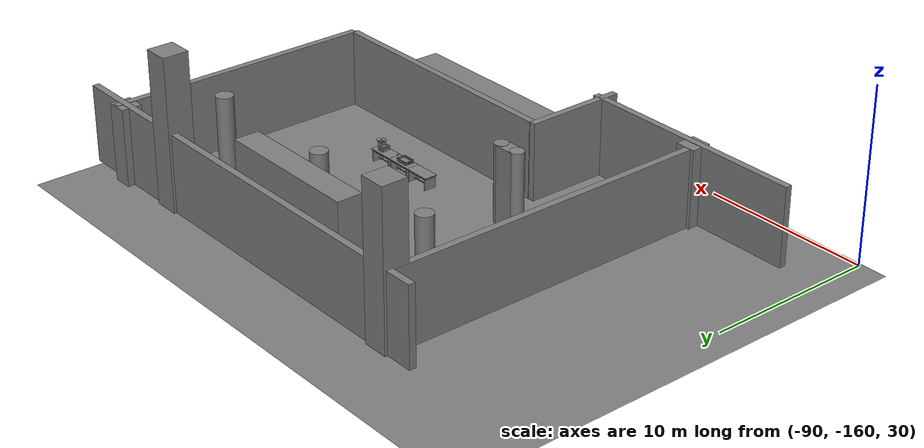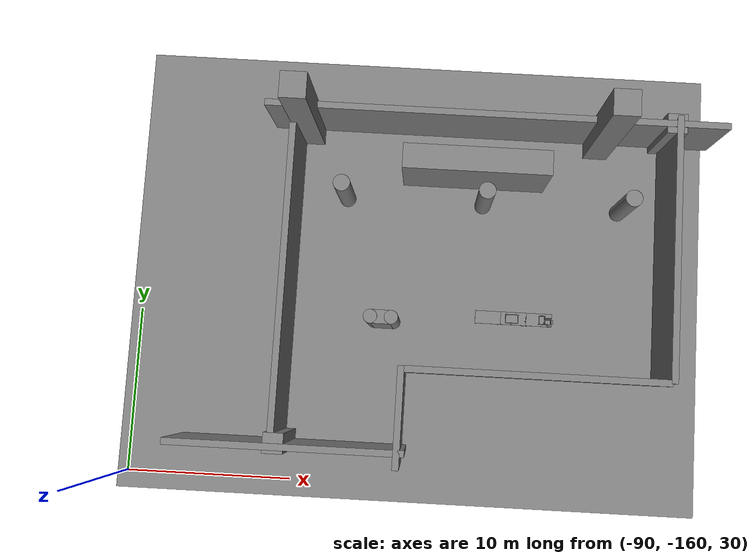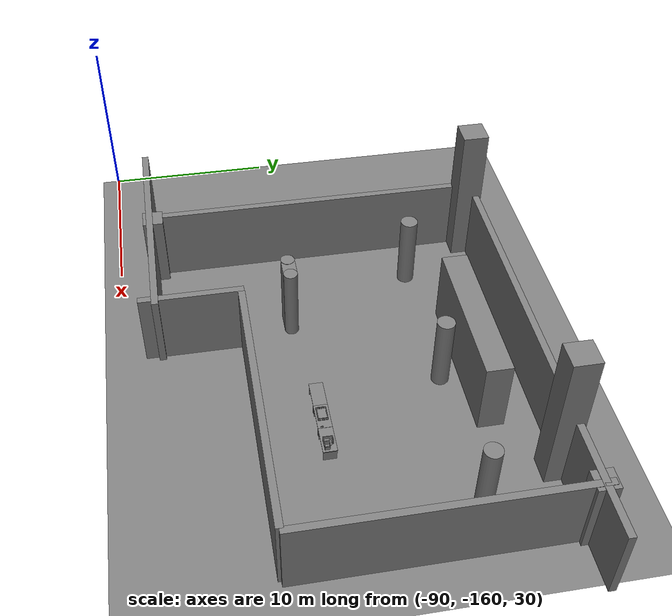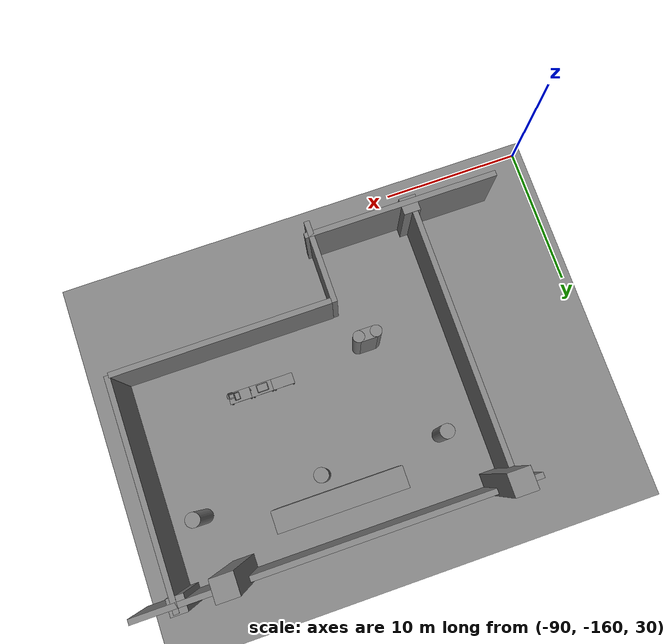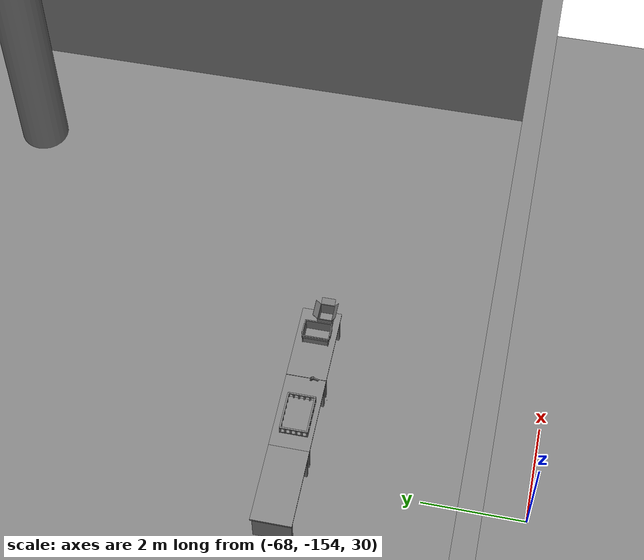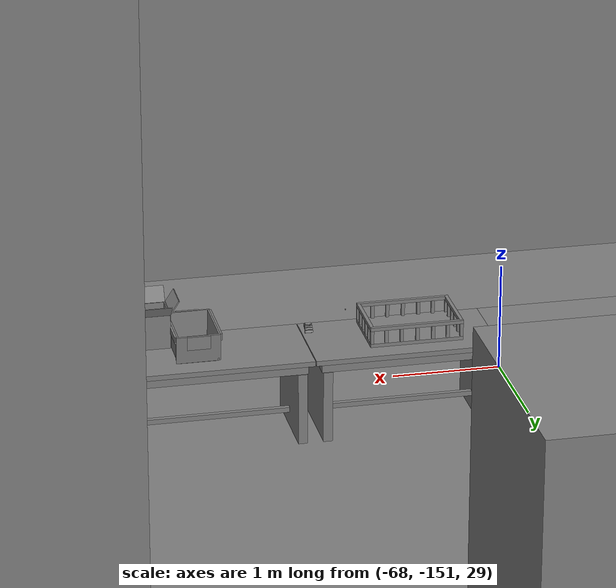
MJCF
<mujoco>
    <option gravity="0.000000000 0.000000000 -9.810000420" timestep="0.0049999999" integrator="implicitfast" density="1.225" viscosity="1.8000001e-05" noslip_iterations="10" iterations="100" sdf_iterations="50">
        <flag multiccd="disable"/>
    </option>
    <size memory="1000M"/>
    <compiler coordinate="local"/>
    <worldbody>
        <light cutoff="30" pos="0 1 1" dir="0 -1 -2"/>
        <light cutoff="30" pos="0 -1 1" dir="0 1 -2"/>
        <body pos="-64.866622925 -149.383972168 30.183746338" euler="89.999992371 89.999946594 0.000000000" name="openloong_gripper_2f85_fix_base_usda_bluebox_01">
            <geom contype="1" conaffinity="1" density="1000" type="box" material="" rgba="0.500000000 0.500000000 0.500000000 1.000000000" solimp="0.899999976 0.949999988 0.001000000" friction="1.000000000 0.005000000 0.000100000" solref="0.020000000 1.000000000" margin="0" condim="3" group="0" pos="0.276596069 0.187225342 0.000061035" quat="0.707107008 0.000077501 0.707106471 0.000077456" size="0.100000001 0.057999998 0.010000000" name="openloong_gripper_2f85_fix_base_usda_geom_A08608B1_C059_4F1A_9F7C_4D3014F894F6"/>
            <geom contype="1" conaffinity="1" density="1000" type="box" material="" rgba="0.500000000 0.500000000 0.500000000 1.000000000" solimp="0.899999976 0.949999988 0.001000000" friction="1.000000000 0.005000000 0.000100000" solref="0.020000000 1.000000000" margin="0" condim="3" group="0" pos="0.000000000 0.002883911 0.000000000" quat="1.000000000 0.000000000 0.000000000 0.000000000" size="0.254000008 0.003000000 0.172000006" name="openloong_gripper_2f85_fix_base_usda_geom_ACE3DD07_93E1_4266_96F7_818F8A47E91F"/>
            <geom contype="1" conaffinity="1" density="1000" type="box" material="" rgba="0.500000000 0.500000000 0.500000000 1.000000000" solimp="0.899999976 0.949999988 0.001000000" friction="1.000000000 0.005000000 0.000100000" solref="0.020000000 1.000000000" margin="0" condim="3" group="0" pos="0.000015259 0.124874115 0.173477173" quat="0.999796450 0.020176515 -0.000000015 0.000000030" size="0.259999990 0.119999997 0.007000000" name="openloong_gripper_2f85_fix_base_usda_geom_9015D250_C60F_44C1_815F_DBD69185C937"/>
            <geom contype="1" conaffinity="1" density="1000" type="box" material="" rgba="0.500000000 0.500000000 0.500000000 1.000000000" solimp="0.899999976 0.949999988 0.001000000" friction="1.000000000 0.005000000 0.000100000" solref="0.020000000 1.000000000" margin="0" condim="3" group="0" pos="0.000015259 0.124874115 -0.173477173" quat="0.999796450 -0.020176545 -0.000000015 0.000000000" size="0.259999990 0.119999997 0.007000000" name="openloong_gripper_2f85_fix_base_usda_geom_B3FAD7EF_8337_4AB8_8BE6_5491646B7C30"/>
            <geom contype="1" conaffinity="1" density="1000" type="box" material="" rgba="0.500000000 0.500000000 0.500000000 1.000000000" solimp="0.899999976 0.949999988 0.001000000" friction="1.000000000 0.005000000 0.000100000" solref="0.020000000 1.000000000" margin="0" condim="3" group="0" pos="0.000015259 0.214012146 0.188980103" quat="0.999913096 0.013176724 0.000000015 0.000000000" size="0.259999990 0.029999999 0.012500000" name="openloong_gripper_2f85_fix_base_usda_geom_13DF218B_EFCF_4350_8C40_EE50BFCE76C6"/>
            <geom contype="1" conaffinity="1" density="1000" type="box" material="" rgba="0.500000000 0.500000000 0.500000000 1.000000000" solimp="0.899999976 0.949999988 0.001000000" friction="1.000000000 0.005000000 0.000100000" solref="0.020000000 1.000000000" margin="0" condim="3" group="0" pos="-0.258346558 0.125289917 0.001876831" quat="0.702796996 -0.020792052 0.710783184 0.020769238" size="0.189999998 0.119999997 0.009000000" name="openloong_gripper_2f85_fix_base_usda_geom_06C5EBFF_E471_4F0B_8104_44F33BEC89AE"/>
            <geom contype="1" conaffinity="1" density="1000" type="box" material="" rgba="0.500000000 0.500000000 0.500000000 1.000000000" solimp="0.899999976 0.949999988 0.001000000" friction="1.000000000 0.005000000 0.000100000" solref="0.020000000 1.000000000" margin="0" condim="3" group="0" pos="0.000015259 0.214012146 -0.188980103" quat="0.999913096 -0.013176769 0.000000030 0.000000015" size="0.259999990 0.029999999 0.012500000" name="openloong_gripper_2f85_fix_base_usda_geom_53A07DA2_0D4B_4FE7_BE75_3E5C7F1E0C9C"/>
            <geom contype="1" conaffinity="1" density="1000" type="box" material="" rgba="0.500000000 0.500000000 0.500000000 1.000000000" solimp="0.899999976 0.949999988 0.001000000" friction="1.000000000 0.005000000 0.000100000" solref="0.020000000 1.000000000" margin="0" condim="3" group="0" pos="-0.276596069 0.187225342 0.000061035" quat="0.707106650 0.000077441 0.707106709 0.000077456" size="0.100000001 0.057999998 0.010000000" name="openloong_gripper_2f85_fix_base_usda_geom_48ED1424_F742_41EC_9247_E0C105B071A8"/>
            <geom contype="1" conaffinity="1" density="1000" type="box" material="" rgba="0.500000000 0.500000000 0.500000000 1.000000000" solimp="0.899999976 0.949999988 0.001000000" friction="1.000000000 0.005000000 0.000100000" solref="0.020000000 1.000000000" margin="0" condim="3" group="0" pos="0.258346558 0.125289917 0.001876831" quat="0.702851534 0.018856451 0.710823834 -0.019329429" size="0.189999998 0.119999997 0.009000000" name="openloong_gripper_2f85_fix_base_usda_geom_034651BC_6FE8_40C3_AB56_5BF214C4134C"/>
            <freejoint name="openloong_gripper_2f85_fix_base_usda_bluebox_01_joint"/>
            <site size="0.005000000 0.005000000 0.005000000" rgba="0.500000000 0.500000000 0.500000000 1.000000000" pos="0.000000000 0.000000000 0.000000000" quat="0.999961913 0.008726534 0.000000000 0.000000000" group="0" type="sphere" name="openloong_gripper_2f85_fix_base_usda_bluebox_01site"/>
        </body>
        <body pos="-64.496299744 -149.491867065 30.235729218" euler="0.000000000 0.000000000 89.999946594" name="openloong_gripper_2f85_fix_base_usda_cardboardbox_01">
            <geom contype="1" conaffinity="1" density="1000" type="box" material="" rgba="0.500000000 0.500000000 0.500000000 1.000000000" solimp="0.899999976 0.949999988 0.001000000" friction="1.000000000 0.005000000 0.000100000" solref="0.020000000 1.000000000" margin="0" condim="3" group="0" pos="-0.003166199 -0.004086494 0.005052090" quat="1.000000000 0.000000000 0.000000000 0.000000000" size="0.142499998 0.177500010 0.005000000" name="openloong_gripper_2f85_fix_base_usda_geom_5DF69B7B_9816_4FAD_8B27_6E54275BB292"/>
            <geom contype="1" conaffinity="1" density="1000" type="box" material="" rgba="0.500000000 0.500000000 0.500000000 1.000000000" solimp="0.899999976 0.949999988 0.001000000" friction="1.000000000 0.005000000 0.000100000" solref="0.020000000 1.000000000" margin="0" condim="3" group="0" pos="-0.003166199 0.170316696 0.150570869" quat="1.000000000 0.000000000 0.000000000 0.000000000" size="0.142499998 0.005000000 0.149999991" name="openloong_gripper_2f85_fix_base_usda_geom_54237394_4BFD_4C51_B93F_2716C84586A6"/>
            <geom contype="1" conaffinity="1" density="1000" type="box" material="" rgba="0.500000000 0.500000000 0.500000000 1.000000000" solimp="0.899999976 0.949999988 0.001000000" friction="1.000000000 0.005000000 0.000100000" solref="0.020000000 1.000000000" margin="0" condim="3" group="0" pos="-0.147399902 -0.005307198 0.150570869" quat="1.000000000 0.000000000 0.000000000 0.000000000" size="0.005000000 0.177500010 0.149999991" name="openloong_gripper_2f85_fix_base_usda_geom_E75DF806_E866_48AC_B701_A97198014F8E"/>
            <geom contype="1" conaffinity="1" density="1000" type="box" material="" rgba="0.500000000 0.500000000 0.500000000 1.000000000" solimp="0.899999976 0.949999988 0.001000000" friction="1.000000000 0.005000000 0.000100000" solref="0.020000000 1.000000000" margin="0" condim="3" group="0" pos="0.140275955 -0.005307198 0.150570869" quat="1.000000000 0.000000000 0.000000000 0.000000000" size="0.005000000 0.177500010 0.149999991" name="openloong_gripper_2f85_fix_base_usda_geom_58BAAD79_CF81_4A07_B007_115F7C9E717C"/>
            <geom contype="1" conaffinity="1" density="1000" type="box" material="" rgba="0.500000000 0.500000000 0.500000000 1.000000000" solimp="0.899999976 0.949999988 0.001000000" friction="1.000000000 0.005000000 0.000100000" solref="0.020000000 1.000000000" margin="0" condim="3" group="0" pos="-0.003166199 -0.181550980 0.150570869" quat="1.000000000 0.000000000 0.000000000 0.000000000" size="0.142499998 0.005000000 0.149999991" name="openloong_gripper_2f85_fix_base_usda_geom_14AC2879_EB06_4233_8EE8_737D47C04AF5"/>
            <freejoint name="openloong_gripper_2f85_fix_base_usda_cardboardbox_01_joint"/>
            <site size="0.005000000 0.005000000 0.005000000" rgba="0.500000000 0.500000000 0.500000000 1.000000000" pos="0.000000000 0.000000000 0.000000000" quat="0.999961913 0.008726535 0.000000000 0.000000000" group="0" type="sphere" name="openloong_gripper_2f85_fix_base_usda_site_6CDB9311_2F99_414D_AF72_0EA37DA9730E"/>
            <body pos="0.139160156 -0.004048347 0.301930904" euler="-179.999954224 49.383502960 179.999954224" name="openloong_gripper_2f85_fix_base_usda_A1_006">
                <geom contype="1" conaffinity="1" density="1000" type="box" material="" rgba="0.500000000 0.500000000 0.500000000 1.000000000" solimp="0.899999976 0.949999988 0.001000000" friction="1.000000000 0.005000000 0.000100000" solref="0.020000000 1.000000000" margin="0" condim="3" group="0" pos="-0.071587563 0.000009537 0.001745224" quat="0.999999881 0.000000000 0.000000000 0.000000000" size="0.071249999 0.179999992 0.002500000" name="openloong_gripper_2f85_fix_base_usda_geom_AECD3309_E70A_4CC8_A785_DEF3BE1328C1"/>
                <joint armature="0" stiffness="0.07" damping="0.0099999998" axis="0.000000 1.000000 0.000000" type="hinge" name="openloong_gripper_2f85_fix_base_usda_A1_006"/>
            </body>
            <body pos="-0.145902634 -0.004086494 0.301938057" euler="-180.000000000 -60.000011444 -180.000000000" name="openloong_gripper_2f85_fix_base_usda_A2_006">
                <geom contype="1" conaffinity="1" density="1000" type="box" material="" rgba="0.500000000 0.500000000 0.500000000 1.000000000" solimp="0.899999976 0.949999988 0.001000000" friction="1.000000000 0.005000000 0.000100000" solref="0.020000000 1.000000000" margin="0" condim="3" group="0" pos="0.071268082 0.000009537 0.002717972" quat="0.000002921 0.000000000 -0.000000030 0.999999881" size="0.071249999 0.179999992 0.002500000" name="openloong_gripper_2f85_fix_base_usda_geom_536E1E35_0E85_4884_9C9D_B9B1BDA3576F"/>
                <joint armature="0" stiffness="0.07" damping="0.0099999998" axis="0.000000 1.000000 0.000000" type="hinge" name="openloong_gripper_2f85_fix_base_usda_A2_006"/>
            </body>
            <body pos="-0.003385544 0.175991058 0.301930904" euler="-125.858116150 -0.000004561 0.000002331" name="openloong_gripper_2f85_fix_base_usda_B2_006">
                <geom contype="1" conaffinity="1" density="1000" type="box" material="" rgba="0.500000000 0.500000000 0.500000000 1.000000000" solimp="0.899999976 0.949999988 0.001000000" friction="1.000000000 0.005000000 0.000100000" solref="0.020000000 1.000000000" margin="0" condim="3" group="0" pos="0.000009537 -0.070939064 -0.002470016" quat="0.999614120 0.027776197 -0.000000015 0.000000030" size="0.137500003 0.064999998 0.005000000" name="openloong_gripper_2f85_fix_base_usda_geom_7FC42894_BC9F_4499_B95A_8E0997D8DD46"/>
                <joint armature="0" stiffness="0.07" damping="0.0099999998" axis="1.000000 0.000000 0.000000" type="hinge" name="openloong_gripper_2f85_fix_base_usda_B2_006"/>
            </body>
            <body pos="-0.003385544 -0.184140205 0.301938057" euler="147.805557251 0.000000000 0.000000000" name="openloong_gripper_2f85_fix_base_usda_B1_006">
                <geom contype="1" conaffinity="1" density="1000" type="box" material="" rgba="0.500000000 0.500000000 0.500000000 1.000000000" solimp="0.899999976 0.949999988 0.001000000" friction="1.000000000 0.005000000 0.000100000" solref="0.020000000 1.000000000" margin="0" condim="3" group="0" pos="-0.000028610 0.070202351 -0.002703667" quat="0.999614179 -0.027776167 0.000000000 0.000000000" size="0.137500003 0.064999998 0.005000000" name="openloong_gripper_2f85_fix_base_usda_geom_CAC64447_06F4_44F6_81F5_8692D8C3F24B"/>
                <joint armature="0" stiffness="0.07" damping="0.0099999998" axis="1.000000 0.000000 0.000000" type="hinge" name="openloong_gripper_2f85_fix_base_usda_B1_006"/>
            </body>
        </body>
        <body pos="-65.882858276 -149.481979370 30.229999542" euler="-64.487716675 0.000000000 0.000000000" name="openloong_gripper_2f85_fix_base_usda_Barcode">
            <geom contype="1" conaffinity="1" density="1000" type="box" material="" rgba="0.500000000 0.500000000 0.500000000 1.000000000" solimp="0.899999976 0.949999988 0.001000000" friction="1.000000000 0.005000000 0.000100000" solref="0.020000000 1.000000000" margin="0" condim="3" group="0" pos="0.000000000 0.013038635 0.001419067" quat="0.000000000 0.000000000 0.000000000 1.000000119" size="0.034000002 0.010000000 0.017999999" name="openloong_gripper_2f85_fix_base_usda_geom_BF85D5B0_1208_4914_ACC9_0F83A13AB794"/>
            <geom contype="1" conaffinity="1" density="1000" type="box" material="" rgba="0.500000000 0.500000000 0.500000000 1.000000000" solimp="0.899999976 0.949999988 0.001000000" friction="1.000000000 0.005000000 0.000100000" solref="0.020000000 1.000000000" margin="0" condim="3" group="0" pos="0.000000000 -0.035301208 -0.007095337" quat="0.000000000 0.000000000 -0.043619365 0.999048233" size="0.028999999 0.010000000 0.020000000" name="openloong_gripper_2f85_fix_base_usda_geom_2CCE409C_08D6_400E_9898_8A4E729C4D31"/>
            <geom contype="1" conaffinity="1" density="1000" type="box" material="" rgba="0.500000000 0.500000000 0.500000000 1.000000000" solimp="0.899999976 0.949999988 0.001000000" friction="1.000000000 0.005000000 0.000100000" solref="0.020000000 1.000000000" margin="0" condim="3" group="0" pos="0.000000000 -0.043411255 -0.011749268" quat="0.922262907 0.386563420 0.000000000 0.000000000" size="0.026000001 0.010000000 0.020000000" name="openloong_gripper_2f85_fix_base_usda_geom_7D24CA26_876B_4D71_A2EC_1F59DE829E79"/>
            <geom contype="1" conaffinity="1" density="1000" type="box" material="" rgba="0.500000000 0.500000000 0.500000000 1.000000000" solimp="0.899999976 0.949999988 0.001000000" friction="1.000000000 0.005000000 0.000100000" solref="0.020000000 1.000000000" margin="0" condim="3" group="0" pos="0.000000000 -0.016967773 -0.031860352" quat="0.000000000 0.000000000 0.000000000 1.000000119" size="0.008000000 0.010000000 0.013000000" name="openloong_gripper_2f85_fix_base_usda_geom_7041ED85_4937_45F7_BABC_558F0AB31EA5"/>
            <geom contype="1" conaffinity="1" density="1000" type="box" material="" rgba="0.500000000 0.500000000 0.500000000 1.000000000" solimp="0.899999976 0.949999988 0.001000000" friction="1.000000000 0.005000000 0.000100000" solref="0.020000000 1.000000000" margin="0" condim="3" group="0" pos="0.000000000 -0.001869202 0.000312805" quat="0.953716993 0.300705761 0.000000000 0.000000000" size="0.032000002 0.010000000 0.018999999" name="openloong_gripper_2f85_fix_base_usda_geom_B5E3546B_A452_47F4_ACD0_970442AD3063"/>
            <geom contype="1" conaffinity="1" density="1000" type="box" material="" rgba="0.500000000 0.500000000 0.500000000 1.000000000" solimp="0.899999976 0.949999988 0.001000000" friction="1.000000000 0.005000000 0.000100000" solref="0.020000000 1.000000000" margin="0" condim="3" group="0" pos="0.000000000 -0.019531250 -0.003173828" quat="0.953716993 0.300705761 0.000000000 0.000000000" size="0.030999999 0.010000000 0.020000000" name="openloong_gripper_2f85_fix_base_usda_geom_F2FDCDA0_7900_448F_A5DF_E6B4B97C4617"/>
            <geom contype="1" conaffinity="1" density="1000" type="box" material="" rgba="0.500000000 0.500000000 0.500000000 1.000000000" solimp="0.899999976 0.949999988 0.001000000" friction="1.000000000 0.005000000 0.000100000" solref="0.020000000 1.000000000" margin="0" condim="3" group="0" pos="0.000000000 -0.035301208 -0.007095337" quat="0.953716993 0.300705761 0.000000000 0.000000000" size="0.028999999 0.010000000 0.020000000" name="openloong_gripper_2f85_fix_base_usda_geom_08E60AFD_B216_42DE_9BBA_0D44B768F095"/>
            <geom contype="1" conaffinity="1" density="1000" type="box" material="" rgba="0.500000000 0.500000000 0.500000000 1.000000000" solimp="0.899999976 0.949999988 0.001000000" friction="1.000000000 0.005000000 0.000100000" solref="0.020000000 1.000000000" margin="0" condim="3" group="0" pos="0.000000000 -0.042617798 -0.071121216" quat="0.000000000 0.000000000 0.000000000 1.000000119" size="0.013000000 0.021000000 0.059999999" name="openloong_gripper_2f85_fix_base_usda_geom_04883A9F_47C2_412D_B8F8_41CC5A572371"/>
            <freejoint name="openloong_gripper_2f85_fix_base_usda_Barcode_joint"/>
            <site size="0.005000000 0.005000000 0.005000000" rgba="0.500000000 0.500000000 0.500000000 1.000000000" pos="0.000000000 0.000000000 0.000000000" quat="1.000000000 0.000000000 0.000000000 0.000000000" group="0" type="sphere" name="openloong_gripper_2f85_fix_base_usda_Barcode_site"/>
        </body>
        <body pos="-66.745018005 -149.392349243 30.184000015" euler="0.000000000 0.000000000 89.999946594" name="[22333506006656]_Basket_01">
            <geom contype="1" conaffinity="1" density="1000" type="box" material="" rgba="0.500000000 0.500000000 0.500000000 1.000000000" solimp="0.899999976 0.949999988 0.001000000" friction="1.000000000 0.005000000 0.000100000" solref="0.020000000 1.000000000" margin="0" condim="3" group="0" pos="-0.052425385 0.389207840 0.089787483" quat="0.707107008 0.000000000 0.000000000 0.707106411" size="0.014249999 0.014249999 0.059999999" name="[22333506006656]_geom_5E4AFC3A_BDE3_4D06_8D4B_E4DE18533C5A"/>
            <geom contype="1" conaffinity="1" density="1000" type="box" material="" rgba="0.500000000 0.500000000 0.500000000 1.000000000" solimp="0.899999976 0.949999988 0.001000000" friction="1.000000000 0.005000000 0.000100000" solref="0.020000000 1.000000000" margin="0" condim="3" group="0" pos="0.264015198 -0.133043289 0.089787483" quat="0.707107008 0.000000000 0.000000000 0.707106411" size="0.014249999 0.014249999 0.059999999" name="[22333506006656]_geom_5ECFC8D8_32F2_4A10_AA27_0094493160DE"/>
            <geom contype="1" conaffinity="1" density="1000" type="box" material="" rgba="0.500000000 0.500000000 0.500000000 1.000000000" solimp="0.899999976 0.949999988 0.001000000" friction="1.000000000 0.005000000 0.000100000" solref="0.020000000 1.000000000" margin="0" condim="3" group="0" pos="-0.264015198 -0.265548706 0.089793205" quat="0.707107008 0.000000000 0.000000000 0.707106411" size="0.014249999 0.014249999 0.059999999" name="[22333506006656]_geom_3BDCF861_AC7F_47EA_AEB8_4026D2FB0D86"/>
            <geom contype="1" conaffinity="1" density="1000" type="box" material="" rgba="0.500000000 0.500000000 0.500000000 1.000000000" solimp="0.899999976 0.949999988 0.001000000" friction="1.000000000 0.005000000 0.000100000" solref="0.020000000 1.000000000" margin="0" condim="3" group="0" pos="-0.160263062 -0.389322281 0.089793205" quat="0.707107008 0.000000000 0.000000000 0.707106411" size="0.014249999 0.014249999 0.059999999" name="[22333506006656]_geom_06BDB276_E9DD_4632_B639_49AF32C24FA4"/>
            <geom contype="1" conaffinity="1" density="1000" type="box" material="" rgba="0.500000000 0.500000000 0.500000000 1.000000000" solimp="0.899999976 0.949999988 0.001000000" friction="1.000000000 0.005000000 0.000100000" solref="0.020000000 1.000000000" margin="0" condim="3" group="0" pos="0.162265778 -0.389322281 0.089787483" quat="0.707107008 0.000000000 0.000000000 0.707106411" size="0.014249999 0.014249999 0.059999999" name="[22333506006656]_geom_33E357A9_6262_4F0F_9B9A_7444E3534206"/>
            <geom contype="1" conaffinity="1" density="1000" type="box" material="" rgba="0.500000000 0.500000000 0.500000000 1.000000000" solimp="0.899999976 0.949999988 0.001000000" friction="1.000000000 0.005000000 0.000100000" solref="0.020000000 1.000000000" margin="0" condim="3" group="0" pos="0.264015198 0.389207840 0.089787483" quat="0.707107008 0.000000000 0.000000000 0.707106411" size="0.014249999 0.014249999 0.059999999" name="[22333506006656]_geom_271D04D7_C6C5_44DC_860E_BF60D311C776"/>
            <geom contype="1" conaffinity="1" density="1000" type="box" material="" rgba="0.500000000 0.500000000 0.500000000 1.000000000" solimp="0.899999976 0.949999988 0.001000000" friction="1.000000000 0.005000000 0.000100000" solref="0.020000000 1.000000000" margin="0" condim="3" group="0" pos="-0.264015198 -0.133043289 0.089793205" quat="0.707107008 0.000000000 0.000000000 0.707106411" size="0.014249999 0.014249999 0.059999999" name="[22333506006656]_geom_476C9CA9_5C3D_4870_91E2_236DE2FD8487"/>
            <geom contype="1" conaffinity="1" density="1000" type="box" material="" rgba="0.500000000 0.500000000 0.500000000 1.000000000" solimp="0.899999976 0.949999988 0.001000000" friction="1.000000000 0.005000000 0.000100000" solref="0.020000000 1.000000000" margin="0" condim="3" group="0" pos="-0.264026642 0.269256592 0.089793205" quat="0.707107008 0.000000000 0.000000000 0.707106411" size="0.014249999 0.014249999 0.059999999" name="[22333506006656]_geom_C8991DEE_CB7B_46F1_BEC8_8CA957634E0A"/>
            <geom contype="1" conaffinity="1" density="1000" type="box" material="" rgba="0.500000000 0.500000000 0.500000000 1.000000000" solimp="0.899999976 0.949999988 0.001000000" friction="1.000000000 0.005000000 0.000100000" solref="0.020000000 1.000000000" margin="0" condim="3" group="0" pos="0.054462433 0.389207840 0.089787483" quat="0.707107008 0.000000000 0.000000000 0.707106411" size="0.014249999 0.014249999 0.059999999" name="[22333506006656]_geom_F8BF127F_C3A6_44E0_B8D9_ED4A7BBFBD8B"/>
            <geom contype="1" conaffinity="1" density="1000" type="box" material="" rgba="0.500000000 0.500000000 0.500000000 1.000000000" solimp="0.899999976 0.949999988 0.001000000" friction="1.000000000 0.005000000 0.000100000" solref="0.020000000 1.000000000" margin="0" condim="3" group="0" pos="0.054462433 -0.389322281 0.089787483" quat="0.707107008 0.000000000 0.000000000 0.707106411" size="0.014249999 0.014249999 0.059999999" name="[22333506006656]_geom_95C21A1B_F6F5_470B_ABEE_0EC1A2CFC838"/>
            <geom contype="1" conaffinity="1" density="1000" type="box" material="" rgba="0.500000000 0.500000000 0.500000000 1.000000000" solimp="0.899999976 0.949999988 0.001000000" friction="1.000000000 0.005000000 0.000100000" solref="0.020000000 1.000000000" margin="0" condim="3" group="0" pos="0.264015198 0.269256592 0.089793205" quat="0.707107008 0.000000000 0.000000000 0.707106411" size="0.014249999 0.014249999 0.059999999" name="[22333506006656]_geom_0BF359CA_76C9_4523_9DC8_2B6A4CC0FD06"/>
            <geom contype="1" conaffinity="1" density="1000" type="box" material="" rgba="0.500000000 0.500000000 0.500000000 1.000000000" solimp="0.899999976 0.949999988 0.001000000" friction="1.000000000 0.005000000 0.000100000" solref="0.020000000 1.000000000" margin="0" condim="3" group="0" pos="0.264015198 -0.389322281 0.089787483" quat="0.707107008 0.000000000 0.000000000 0.707106411" size="0.014249999 0.014249999 0.059999999" name="[22333506006656]_geom_4FD9298A_D1A7_4FB3_A78A_846FE05BC40D"/>
            <geom contype="1" conaffinity="1" density="1000" type="box" material="" rgba="0.500000000 0.500000000 0.500000000 1.000000000" solimp="0.899999976 0.949999988 0.001000000" friction="1.000000000 0.005000000 0.000100000" solref="0.020000000 1.000000000" margin="0" condim="3" group="0" pos="0.000000000 0.000000000 0.015998840" quat="0.707107008 0.000000000 0.000000000 0.707106411" size="0.403499991 0.279000014 0.015750000" name="[22333506006656]_geom_AE545FC0_875C_4B91_A1C7_9B0D446F04E0"/>
            <geom contype="1" conaffinity="1" density="1000" type="box" material="" rgba="0.500000000 0.500000000 0.500000000 1.000000000" solimp="0.899999976 0.949999988 0.001000000" friction="1.000000000 0.005000000 0.000100000" solref="0.020000000 1.000000000" margin="0" condim="3" group="0" pos="0.000000000 -0.389476776 0.163619041" quat="0.707107008 0.000000000 0.000000000 0.707106411" size="0.015000000 0.277500004 0.015750000" name="[22333506006656]_geom_7F06D1E5_4717_43CE_A1CA_60DCCF9246E1"/>
            <geom contype="1" conaffinity="1" density="1000" type="box" material="" rgba="0.500000000 0.500000000 0.500000000 1.000000000" solimp="0.899999976 0.949999988 0.001000000" friction="1.000000000 0.005000000 0.000100000" solref="0.020000000 1.000000000" margin="0" condim="3" group="0" pos="0.162265778 0.389207840 0.089787483" quat="0.707107008 0.000000000 0.000000000 0.707106411" size="0.014249999 0.014249999 0.059999999" name="[22333506006656]_geom_460756EE_5ADC_49F2_99AB_E08C9BD23450"/>
            <geom contype="1" conaffinity="1" density="1000" type="box" material="" rgba="0.500000000 0.500000000 0.500000000 1.000000000" solimp="0.899999976 0.949999988 0.001000000" friction="1.000000000 0.005000000 0.000100000" solref="0.020000000 1.000000000" margin="0" condim="3" group="0" pos="0.000000000 0.389471054 0.163619041" quat="0.707107008 0.000000000 0.000000000 0.707106411" size="0.015000000 0.277500004 0.015750000" name="[22333506006656]_geom_08902F75_77CC_4E82_A1DC_527F5EABAD0D"/>
            <geom contype="1" conaffinity="1" density="1000" type="box" material="" rgba="0.500000000 0.500000000 0.500000000 1.000000000" solimp="0.899999976 0.949999988 0.001000000" friction="1.000000000 0.005000000 0.000100000" solref="0.020000000 1.000000000" margin="0" condim="3" group="0" pos="-0.263511658 0.000000000 0.163619041" quat="0.707107008 0.000000000 0.000000000 0.707106411" size="0.403499991 0.015000000 0.015750000" name="[22333506006656]_geom_E6401EA3_DB7D_49D5_8EB7_0755E8721113"/>
            <geom contype="1" conaffinity="1" density="1000" type="box" material="" rgba="0.500000000 0.500000000 0.500000000 1.000000000" solimp="0.899999976 0.949999988 0.001000000" friction="1.000000000 0.005000000 0.000100000" solref="0.020000000 1.000000000" margin="0" condim="3" group="0" pos="-0.264015198 0.141334534 0.089793205" quat="0.707107008 0.000000000 0.000000000 0.707106411" size="0.014249999 0.014249999 0.059999999" name="[22333506006656]_geom_AB1953CA_D8EA_4D42_A21A_E60FA0F352C1"/>
            <geom contype="1" conaffinity="1" density="1000" type="box" material="" rgba="0.500000000 0.500000000 0.500000000 1.000000000" solimp="0.899999976 0.949999988 0.001000000" friction="1.000000000 0.005000000 0.000100000" solref="0.020000000 1.000000000" margin="0" condim="3" group="0" pos="0.264015198 -0.265548706 0.089787483" quat="0.707107008 0.000000000 0.000000000 0.707106411" size="0.014249999 0.014249999 0.059999999" name="[22333506006656]_geom_C008D872_3D9B_415D_9558_6404F1A30C84"/>
            <geom contype="1" conaffinity="1" density="1000" type="box" material="" rgba="0.500000000 0.500000000 0.500000000 1.000000000" solimp="0.899999976 0.949999988 0.001000000" friction="1.000000000 0.005000000 0.000100000" solref="0.020000000 1.000000000" margin="0" condim="3" group="0" pos="-0.160263062 0.389207840 0.089787483" quat="0.707107008 0.000000000 0.000000000 0.707106411" size="0.014249999 0.014249999 0.059999999" name="[22333506006656]_geom_D00DBAEE_69CD_43F9_87E6_9F6100E226D1"/>
            <geom contype="1" conaffinity="1" density="1000" type="box" material="" rgba="0.500000000 0.500000000 0.500000000 1.000000000" solimp="0.899999976 0.949999988 0.001000000" friction="1.000000000 0.005000000 0.000100000" solref="0.020000000 1.000000000" margin="0" condim="3" group="0" pos="-0.052425385 -0.389322281 0.089787483" quat="0.707107008 0.000000000 0.000000000 0.707106411" size="0.014249999 0.014249999 0.059999999" name="[22333506006656]_geom_1710B3FC_61E8_4BE4_99F7_2FA7DE11FD40"/>
            <geom contype="1" conaffinity="1" density="1000" type="box" material="" rgba="0.500000000 0.500000000 0.500000000 1.000000000" solimp="0.899999976 0.949999988 0.001000000" friction="1.000000000 0.005000000 0.000100000" solref="0.020000000 1.000000000" margin="0" condim="3" group="0" pos="-0.264026642 -0.389322281 0.089793205" quat="0.707107008 0.000000000 0.000000000 0.707106411" size="0.014249999 0.014249999 0.059999999" name="[22333506006656]_geom_E76558F1_3279_4BF1_B857_D786837EAE2A"/>
            <geom contype="1" conaffinity="1" density="1000" type="box" material="" rgba="0.500000000 0.500000000 0.500000000 1.000000000" solimp="0.899999976 0.949999988 0.001000000" friction="1.000000000 0.005000000 0.000100000" solref="0.020000000 1.000000000" margin="0" condim="3" group="0" pos="0.264015198 0.141334534 0.089787483" quat="0.707107008 0.000000000 0.000000000 0.707106411" size="0.014249999 0.014249999 0.059999999" name="[22333506006656]_geom_79F52955_0561_44A6_ACBB_D9CB5D1475EE"/>
            <geom contype="1" conaffinity="1" density="1000" type="box" material="" rgba="0.500000000 0.500000000 0.500000000 1.000000000" solimp="0.899999976 0.949999988 0.001000000" friction="1.000000000 0.005000000 0.000100000" solref="0.020000000 1.000000000" margin="0" condim="3" group="0" pos="-0.264015198 0.389207840 0.089793205" quat="0.707107008 0.000000000 0.000000000 0.707106411" size="0.014249999 0.014249999 0.059999999" name="[22333506006656]_geom_03485B37_F7C3_4D42_94B0_B4C058161EF0"/>
            <geom contype="1" conaffinity="1" density="1000" type="box" material="" rgba="0.500000000 0.500000000 0.500000000 1.000000000" solimp="0.899999976 0.949999988 0.001000000" friction="1.000000000 0.005000000 0.000100000" solref="0.020000000 1.000000000" margin="0" condim="3" group="0" pos="0.264015198 0.004480362 0.089787483" quat="0.707107008 0.000000000 0.000000000 0.707106411" size="0.014249999 0.014249999 0.059999999" name="[22333506006656]_geom_899C837B_E847_4CC5_886F_D4BC3C68F79B"/>
            <geom contype="1" conaffinity="1" density="1000" type="box" material="" rgba="0.500000000 0.500000000 0.500000000 1.000000000" solimp="0.899999976 0.949999988 0.001000000" friction="1.000000000 0.005000000 0.000100000" solref="0.020000000 1.000000000" margin="0" condim="3" group="0" pos="0.263694763 -0.000011444 0.163619041" quat="0.707107008 0.000000000 0.000000000 0.707106411" size="0.403499991 0.015000000 0.015750000" name="[22333506006656]_geom_F2C5C548_FD4D_4FDC_ABB2_3897F4524914"/>
            <geom contype="1" conaffinity="1" density="1000" type="box" material="" rgba="0.500000000 0.500000000 0.500000000 1.000000000" solimp="0.899999976 0.949999988 0.001000000" friction="1.000000000 0.005000000 0.000100000" solref="0.020000000 1.000000000" margin="0" condim="3" group="0" pos="-0.264015198 0.004480362 0.089793205" quat="0.707107008 0.000000000 0.000000000 0.707106411" size="0.014249999 0.014249999 0.059999999" name="[22333506006656]_geom_F298C54D_A577_4C1E_AA52_BE71B9C26C21"/>
            <freejoint name="[22333506006656]_joint_4B84A3C9_E3EB_4D44_BD31_B4F91E99A6CD"/>
        </body>
        <body pos="0.000000000 0.000000000 0.000000000" euler="0.000000000 0.000000000 0.000000000" name="Static Objects_Static Objects">
            <geom contype="1" conaffinity="1" density="1000" type="box" material="" rgba="0.500000000 0.500000000 0.500000000 1.000000000" solimp="0.899999976 0.949999988 0.001000000" friction="1.000000000 0.005000000 0.000100000" solref="0.020000000 1.000000000" margin="0" condim="3" group="0" pos="-67.544113159 -149.365814209 29.727830887" quat="0.500000417 0.499999970 0.499999553 0.499999970" size="0.381000012 0.319999993 0.041000001" name="Static Objects_geom_374FF377_BF5B_4718_9B5B_EC2085A73517"/>
            <geom contype="1" conaffinity="1" density="1000" type="box" material="" rgba="0.500000000 0.500000000 0.500000000 1.000000000" solimp="0.899999976 0.949999988 0.001000000" friction="1.000000000 0.005000000 0.000100000" solref="0.020000000 1.000000000" margin="0" condim="3" group="0" pos="-68.239501953 -149.365814209 30.086868286" quat="0.500000417 0.499999970 0.499999553 0.499999970" size="0.370999992 0.039500002 0.745000005" name="Static Objects_geom_83EA29C1_74C5_44FF_ABE2_8F25D8EBD015"/>
            <geom contype="1" conaffinity="1" density="1000" type="box" material="" rgba="0.500000000 0.500000000 0.500000000 1.000000000" solimp="0.899999976 0.949999988 0.001000000" friction="1.000000000 0.005000000 0.000100000" solref="0.020000000 1.000000000" margin="0" condim="3" group="0" pos="-68.239501953 -149.365814209 30.147235870" quat="0.500000417 0.499999970 0.499999553 0.499999970" size="0.400000006 0.022000000 0.800000012" name="Static Objects_geom_48D31C3E_6BFE_49F0_AD6F_8DB56E4CA5F3"/>
            <geom contype="1" conaffinity="1" density="1000" type="box" material="" rgba="0.500000000 0.500000000 0.500000000 1.000000000" solimp="0.899999976 0.949999988 0.001000000" friction="1.000000000 0.005000000 0.000100000" solref="0.020000000 1.000000000" margin="0" condim="3" group="0" pos="-68.934890747 -149.365814209 29.727830887" quat="0.500000417 0.499999970 0.499999553 0.499999970" size="0.381000012 0.319999993 0.041000001" name="Static Objects_geom_3889476C_9EC9_4DB2_989D_EA5E8DB19668"/>
            <geom contype="1" conaffinity="1" density="1000" type="box" material="" rgba="0.500000000 0.500000000 0.500000000 1.000000000" solimp="0.899999976 0.949999988 0.001000000" friction="1.000000000 0.005000000 0.000100000" solref="0.020000000 1.000000000" margin="0" condim="3" group="0" pos="-68.239501953 -149.365814209 29.561563492" quat="0.500000417 0.499999970 0.499999553 0.499999970" size="0.020000000 0.022000000 0.660000026" name="Static Objects_geom_AB079554_B30F_49EC_BD2D_7C37FDFEED88"/>
            <geom contype="1" conaffinity="1" density="1000" type="box" material="" rgba="0.500000000 0.500000000 0.500000000 1.000000000" solimp="0.899999976 0.949999988 0.001000000" friction="1.000000000 0.005000000 0.000100000" solref="0.020000000 1.000000000" margin="0" condim="3" group="0" pos="-65.945671082 -149.365814209 29.727830887" quat="0.500000417 0.499999970 0.499999553 0.499999970" size="0.381000012 0.319999993 0.041000001" name="Static Objects_geom_4367107A_0719_4340_AF6D_7B773DE6B604"/>
            <geom contype="1" conaffinity="1" density="1000" type="box" material="" rgba="0.500000000 0.500000000 0.500000000 1.000000000" solimp="0.899999976 0.949999988 0.001000000" friction="1.000000000 0.005000000 0.000100000" solref="0.020000000 1.000000000" margin="0" condim="3" group="0" pos="-66.641059875 -149.365814209 30.086868286" quat="0.500000417 0.499999970 0.499999553 0.499999970" size="0.370999992 0.039500002 0.745000005" name="Static Objects_geom_FA669725_FAEA_4BA7_AE02_66A91788479B"/>
            <geom contype="1" conaffinity="1" density="1000" type="box" material="" rgba="0.500000000 0.500000000 0.500000000 1.000000000" solimp="0.899999976 0.949999988 0.001000000" friction="1.000000000 0.005000000 0.000100000" solref="0.020000000 1.000000000" margin="0" condim="3" group="0" pos="-66.641059875 -149.365814209 30.147235870" quat="0.500000417 0.499999970 0.499999553 0.499999970" size="0.400000006 0.022000000 0.800000012" name="Static Objects_geom_221545A1_0B84_41A1_AB66_4A54B0DC961A"/>
            <geom contype="1" conaffinity="1" density="1000" type="box" material="" rgba="0.500000000 0.500000000 0.500000000 1.000000000" solimp="0.899999976 0.949999988 0.001000000" friction="1.000000000 0.005000000 0.000100000" solref="0.020000000 1.000000000" margin="0" condim="3" group="0" pos="-67.336448669 -149.365814209 29.727830887" quat="0.500000417 0.499999970 0.499999553 0.499999970" size="0.381000012 0.319999993 0.041000001" name="Static Objects_geom_AC62C5DD_9EA7_4697_BAD1_B6D505AB9784"/>
            <geom contype="1" conaffinity="1" density="1000" type="box" material="" rgba="0.500000000 0.500000000 0.500000000 1.000000000" solimp="0.899999976 0.949999988 0.001000000" friction="1.000000000 0.005000000 0.000100000" solref="0.020000000 1.000000000" margin="0" condim="3" group="0" pos="-66.641059875 -149.365814209 29.561563492" quat="0.500000417 0.499999970 0.499999553 0.499999970" size="0.020000000 0.022000000 0.660000026" name="Static Objects_geom_66F7F768_055B_4C58_AA8C_0143754773DA"/>
            <geom contype="1" conaffinity="1" density="1000" type="box" material="" rgba="0.500000000 0.500000000 0.500000000 1.000000000" solimp="0.899999976 0.949999988 0.001000000" friction="1.000000000 0.005000000 0.000100000" solref="0.020000000 1.000000000" margin="0" condim="3" group="0" pos="-64.338577271 -149.365814209 29.727830887" quat="0.500000417 0.499999970 0.499999553 0.499999970" size="0.381000012 0.319999993 0.041000001" name="Static Objects_geom_2B9004C4_AE7C_4F63_B35C_07D4D2B95D35"/>
            <geom contype="1" conaffinity="1" density="1000" type="box" material="" rgba="0.500000000 0.500000000 0.500000000 1.000000000" solimp="0.899999976 0.949999988 0.001000000" friction="1.000000000 0.005000000 0.000100000" solref="0.020000000 1.000000000" margin="0" condim="3" group="0" pos="-65.033966064 -149.365814209 30.086868286" quat="0.500000417 0.499999970 0.499999553 0.499999970" size="0.370999992 0.039500002 0.745000005" name="Static Objects_geom_7AA0E23E_89EB_40F5_A401_465121DEB00C"/>
            <geom contype="1" conaffinity="1" density="1000" type="box" material="" rgba="0.500000000 0.500000000 0.500000000 1.000000000" solimp="0.899999976 0.949999988 0.001000000" friction="1.000000000 0.005000000 0.000100000" solref="0.020000000 1.000000000" margin="0" condim="3" group="0" pos="-65.033966064 -149.365814209 30.147235870" quat="0.500000417 0.499999970 0.499999553 0.499999970" size="0.400000006 0.022000000 0.800000012" name="Static Objects_geom_3388880D_7A4F_4154_AFB7_3935AAFA4923"/>
            <geom contype="1" conaffinity="1" density="1000" type="box" material="" rgba="0.500000000 0.500000000 0.500000000 1.000000000" solimp="0.899999976 0.949999988 0.001000000" friction="1.000000000 0.005000000 0.000100000" solref="0.020000000 1.000000000" margin="0" condim="3" group="0" pos="-65.729354858 -149.365814209 29.727830887" quat="0.500000417 0.499999970 0.499999553 0.499999970" size="0.381000012 0.319999993 0.041000001" name="Static Objects_geom_A37402A4_F263_481D_8CB7_7D43D363B4D7"/>
            <geom contype="1" conaffinity="1" density="1000" type="box" material="" rgba="0.500000000 0.500000000 0.500000000 1.000000000" solimp="0.899999976 0.949999988 0.001000000" friction="1.000000000 0.005000000 0.000100000" solref="0.020000000 1.000000000" margin="0" condim="3" group="0" pos="-65.033966064 -149.365814209 29.561563492" quat="0.500000417 0.499999970 0.499999553 0.499999970" size="0.020000000 0.022000000 0.660000026" name="Static Objects_geom_74E856F4_99CF_4038_9594_7F837C6E54A3"/>
            <geom contype="1" conaffinity="1" density="1000" type="box" material="" rgba="0.500000000 0.500000000 0.500000000 1.000000000" solimp="0.899999976 0.949999988 0.001000000" friction="1.000000000 0.005000000 0.000100000" solref="0.020000000 1.000000000" margin="0" condim="3" group="0" pos="-61.754566193 -137.853729248 33.906845093" quat="0.707107067 0.000000000 0.000000000 0.707106471" size="0.759999990 0.759999990 4.500000000" name="Static Objects_geom_347B2EF8_C8EF_40E0_A1E9_543E2ABC753D"/>
            <geom contype="1" conaffinity="1" density="1000" type="box" material="" rgba="0.500000000 0.500000000 0.500000000 1.000000000" solimp="0.899999976 0.949999988 0.001000000" friction="1.000000000 0.005000000 0.000100000" solref="0.020000000 1.000000000" margin="0" condim="3" group="0" pos="-57.511135101 -144.927108765 31.707921982" quat="1.000000000 0.000000000 0.000000000 0.000000000" size="0.200000003 8.000000000 2.299999952" name="Static Objects_geom_97A24345_676E_441B_B0C0_F22D6DD6E85C"/>
            <geom contype="1" conaffinity="1" density="1000" type="box" material="" rgba="0.500000000 0.500000000 0.500000000 1.000000000" solimp="0.899999976 0.949999988 0.001000000" friction="1.000000000 0.005000000 0.000100000" solref="0.020000000 1.000000000" margin="0" condim="3" group="0" pos="-80.517646790 -157.574050903 31.688196182" quat="0.707107067 0.000000000 0.000000000 0.707106471" size="0.600000024 0.600000024 2.299999952" name="Static Objects_geom_D2959398_DA23_4ADF_9B46_0C718E6239A3"/>
            <geom contype="1" conaffinity="1" density="1000" type="box" material="" rgba="0.500000000 0.500000000 0.500000000 1.000000000" solimp="0.899999976 0.949999988 0.001000000" friction="1.000000000 0.005000000 0.000100000" solref="0.020000000 1.000000000" margin="0" condim="3" group="0" pos="-80.711044312 -147.414932251 31.666158676" quat="1.000000000 0.000000000 0.000000000 0.000000000" size="0.200000003 10.000000000 2.299999952" name="Static Objects_geom_9DD97B8C_105F_40AC_8981_D0F0C9691CEE"/>
            <geom contype="1" conaffinity="1" density="1000" type="box" material="" rgba="0.500000000 0.500000000 0.500000000 1.000000000" solimp="0.899999976 0.949999988 0.001000000" friction="1.000000000 0.005000000 0.000100000" solref="0.020000000 1.000000000" margin="0" condim="3" group="0" pos="-57.687217712 -137.434692383 31.688196182" quat="0.707107067 0.000000000 0.000000000 0.707106471" size="0.600000024 0.600000024 2.299999952" name="Static Objects_geom_B06313F1_BE3C_47A6_B6B0_1443FEF3639A"/>
            <geom contype="1" conaffinity="1" density="1000" type="box" material="" rgba="0.500000000 0.500000000 0.500000000 1.000000000" solimp="0.899999976 0.949999988 0.001000000" friction="1.000000000 0.005000000 0.000100000" solref="0.020000000 1.000000000" margin="0" condim="3" group="0" pos="-69.537033081 -140.263229370 31.714921951" quat="0.707107067 0.000000000 0.000000000 0.707106471" size="0.759999990 4.500000000 2.299999952" name="Static Objects_geom_659380F9_717C_4F3D_9B24_554FD27C62EE"/>
            <geom contype="1" conaffinity="1" density="1000" type="box" material="" rgba="0.500000000 0.500000000 0.500000000 1.000000000" solimp="0.899999976 0.949999988 0.001000000" friction="1.000000000 0.005000000 0.000100000" solref="0.020000000 1.000000000" margin="0" condim="3" group="0" pos="-80.073638916 -137.853713989 33.906845093" quat="0.707107067 0.000000000 0.000000000 0.707106471" size="0.759999990 0.759999990 4.500000000" name="Static Objects_geom_20318C7B_4A78_413C_9141_DCD14ADD85A4"/>
            <geom contype="1" conaffinity="1" density="1000" type="box" material="" rgba="0.500000000 0.500000000 0.500000000 1.000000000" solimp="0.899999976 0.949999988 0.001000000" friction="1.000000000 0.005000000 0.000100000" solref="0.020000000 1.000000000" margin="0" condim="3" group="0" pos="-73.406707764 -155.734664917 31.707921982" quat="1.000000000 0.000000000 0.000000000 0.000000000" size="0.200000003 3.000000000 2.299999952" name="Static Objects_geom_04481F6B_339B_4402_A747_BDFA1182ABF0"/>
            <geom contype="1" conaffinity="1" density="1000" type="box" material="" rgba="0.500000000 0.500000000 0.500000000 1.000000000" solimp="0.899999976 0.949999988 0.001000000" friction="1.000000000 0.005000000 0.000100000" solref="0.020000000 1.000000000" margin="0" condim="3" group="0" pos="-68.497543335 -137.448257446 31.707921982" quat="0.707107067 0.000000000 0.000000000 0.707106471" size="0.200000003 14.000000000 2.299999952" name="Static Objects_geom_97BFD308_9635_485E_8EB3_27F2EAA58ED6"/>
            <geom contype="1" conaffinity="1" density="1000" type="cylinder" material="" rgba="0.500000000 0.500000000 0.500000000 1.000000000" solimp="0.899999976 0.949999988 0.001000000" friction="1.000000000 0.005000000 0.000100000" solref="0.020000000 1.000000000" margin="0" condim="3" group="0" pos="-68.868522644 -142.134506226 31.711090088" quat="0.707107067 0.000000000 0.000000000 0.707106471" size="0.509999990 2.299999952 1.000000000" name="Static Objects_geom_55397F92_5BA9_4EAB_A083_7E37B489E1EA"/>
            <geom contype="1" conaffinity="1" density="1000" type="plane" material="" rgba="0.500000000 0.500000000 0.500000000 1.000000000" solimp="0.899999976 0.949999988 0.001000000" friction="1.000000000 0.005000000 0.000100000" solref="0.020000000 1.000000000" margin="0" condim="3" group="0" pos="-72.873703003 -147.131927490 29.409669876" quat="1.000000000 0.000000000 0.000000000 0.000000000" size="18.000000000 14.000000000 1.000000000" name="Static Objects_geom_815E07B4_0C23_4CC9_8A11_D4696041B176"/>
            <geom contype="1" conaffinity="1" density="1000" type="box" material="" rgba="0.500000000 0.500000000 0.500000000 1.000000000" solimp="0.899999976 0.949999988 0.001000000" friction="1.000000000 0.005000000 0.000100000" solref="0.020000000 1.000000000" margin="0" condim="3" group="0" pos="-79.943580627 -157.782272339 31.707921982" quat="0.707107067 0.000000000 0.000000000 0.707106471" size="0.200000003 7.000000000 2.299999952" name="Static Objects_geom_D56F2A4C_A537_4382_A850_EB57F26BD425"/>
            <geom contype="1" conaffinity="1" density="1000" type="box" material="" rgba="0.500000000 0.500000000 0.500000000 1.000000000" solimp="0.899999976 0.949999988 0.001000000" friction="1.000000000 0.005000000 0.000100000" solref="0.020000000 1.000000000" margin="0" condim="3" group="0" pos="-65.421028137 -152.903442383 31.707921982" quat="0.707107067 0.000000000 0.000000000 0.707106471" size="0.200000003 7.800000191 2.299999952" name="Static Objects_geom_114ACD90_A15E_4085_8D26_48172F2D993A"/>
            <geom contype="1" conaffinity="1" density="1000" type="box" material="" rgba="0.500000000 0.500000000 0.500000000 1.000000000" solimp="0.899999976 0.949999988 0.001000000" friction="1.000000000 0.005000000 0.000100000" solref="0.020000000 1.000000000" margin="0" condim="3" group="0" pos="-74.776908875 -149.964416504 31.688196182" quat="1.000000000 0.000000000 0.000000000 0.000000000" size="0.600000024 0.409999996 2.299999952" name="Static Objects_geom_CA40612B_8851_481D_8C29_DDCA633033D5"/>
            <geom contype="1" conaffinity="1" density="1000" type="cylinder" material="" rgba="0.500000000 0.500000000 0.500000000 1.000000000" solimp="0.899999976 0.949999988 0.001000000" friction="1.000000000 0.005000000 0.000100000" solref="0.020000000 1.000000000" margin="0" condim="3" group="0" pos="-60.161884308 -142.134506226 31.711090088" quat="0.707107067 0.000000000 0.000000000 0.707106471" size="0.509999990 2.299999952 1.000000000" name="Static Objects_geom_C4CD42C1_5282_4AF7_B8DF_125750EA161F"/>
            <geom contype="1" conaffinity="1" density="1000" type="cylinder" material="" rgba="0.500000000 0.500000000 0.500000000 1.000000000" solimp="0.899999976 0.949999988 0.001000000" friction="1.000000000 0.005000000 0.000100000" solref="0.020000000 1.000000000" margin="0" condim="3" group="0" pos="-75.382453918 -149.963455200 31.711090088" quat="0.707107067 0.000000000 0.000000000 0.707106471" size="0.409999996 2.299999952 1.000000000" name="Static Objects_geom_83903A36_1525_4ED9_A3D9_353C0DEDD7C6"/>
            <geom contype="1" conaffinity="1" density="1000" type="cylinder" material="" rgba="0.500000000 0.500000000 0.500000000 1.000000000" solimp="0.899999976 0.949999988 0.001000000" friction="1.000000000 0.005000000 0.000100000" solref="0.020000000 1.000000000" margin="0" condim="3" group="0" pos="-74.154960632 -149.963455200 31.711090088" quat="0.707107067 0.000000000 0.000000000 0.707106471" size="0.409999996 2.299999952 1.000000000" name="Static Objects_geom_215313B1_23B1_4936_BDBE_DE9645B980BB"/>
            <geom contype="1" conaffinity="1" density="1000" type="cylinder" material="" rgba="0.500000000 0.500000000 0.500000000 1.000000000" solimp="0.899999976 0.949999988 0.001000000" friction="1.000000000 0.005000000 0.000100000" solref="0.020000000 1.000000000" margin="0" condim="3" group="0" pos="-77.566612244 -142.134506226 31.711090088" quat="0.707107067 0.000000000 0.000000000 0.707106471" size="0.509999990 2.299999952 1.000000000" name="Static Objects_geom_775C5FFF_CE63_4492_AD26_7F4ECEF78A9D"/>
        </body>
        <body pos="-66.291030884 -149.869689941 29.018842697" euler="0.000000000 0.000000000 89.999946594" mocap="true" name="openloong_gripper_2f85_fix_base_usda_leftHandMocap"/>
        <body pos="-66.291030884 -149.869689941 29.018842697" euler="0.000000000 0.000000000 89.999946594" mocap="true" name="openloong_gripper_2f85_fix_base_usda_rightHandMocap"/>
        <body pos="-66.291030884 -149.869689941 30.218843460" euler="0.000000000 0.000000000 89.999946594" name="openloong_gripper_2f85_fix_base_usda_base_link">
            <geom contype="1" conaffinity="1" density="1000" type="mesh" material="" rgba="0.783999979 0.783999979 0.783999979 1.000000000" solimp="0.899999976 0.949999988 0.001000000" friction="1.000000000 0.005000000 0.000100000" solref="0.020000000 1.000000000" margin="0" condim="3" group="3" mesh="base_link" pos="0.000000000 0.000000000 0.000000000" quat="1.000000000 0.000000000 0.000000000 0.000000000" size="1.000000000 1.000000000 1.000000000" name="openloong_gripper_2f85_fix_base_usda__geom_7_0E685109_D8B2_4E36_BE1E_505732E44D0E"/>
            <site size="0.005000000 0.005000000 0.005000000" rgba="0.500000000 0.500000000 0.500000000 1.000000000" pos="0.000000000 0.000000000 0.000000000" quat="1.000000000 0.000000000 0.000000000 0.000000000" group="0" type="sphere" name="openloong_gripper_2f85_fix_base_usda_imu"/>
            <inertial mass="22.447001" pos="-0.005664100 -0.001336700 0.238289997" diaginertia="0.374352545 0.277180195 0.220617250" quat="0.999247074 0.035235517 -0.015086859 0.006023135"/>
            <body pos="0.000000000 0.000000000 0.299997330" euler="0.000000000 0.000000000 0.000000000" name="openloong_gripper_2f85_fix_base_usda_dummy_body">
                <geom contype="1" conaffinity="1" density="1000" type="sphere" material="" rgba="0.783999979 0.783999979 0.783999979 1.000000000" solimp="0.899999976 0.949999988 0.001000000" friction="1.000000000 0.005000000 0.000100000" solref="0.020000000 1.000000000" margin="0" condim="3" group="3" pos="0.000000000 0.000000000 0.000000000" quat="1.000000000 0.000000000 0.000000000 0.000000000" size="0.010000000 0.000000000 0.000000000" name="openloong_gripper_2f85_fix_base_usda__geom_8_4ACE4A30_9B49_4D62_A1EA_E3D74FB6EB17"/>
                <joint armature="0.0099999998" stiffness="0" damping="0.1" axis="0.000000 0.000000 1.000000" type="hinge" name="openloong_gripper_2f85_fix_base_usda_dummy_joint"/>
                <site size="0.010000000 0.005000000 0.005000000" rgba="0.500000000 0.500000000 0.500000000 1.000000000" pos="0.000000000 0.000000000 0.000000000" quat="1.000000000 0.000000000 0.000000000 0.000000000" group="3" type="sphere" name="openloong_gripper_2f85_fix_base_usda_dummy_site"/>
            </body>
            <body pos="0.009002686 0.000000000 0.406400681" euler="0.000000000 0.000000000 0.000000000" name="openloong_gripper_2f85_fix_base_usda_Link_head_yaw">
                <geom contype="1" conaffinity="1" density="1000" type="mesh" material="" rgba="0.783999979 0.783999979 0.783999979 1.000000000" solimp="0.899999976 0.949999988 0.001000000" friction="1.000000000 0.005000000 0.000100000" solref="0.020000000 1.000000000" margin="0" condim="3" group="3" mesh="Link_head_yaw" pos="0.000000000 0.000000000 0.000000000" quat="1.000000000 0.000000000 0.000000000 0.000000000" size="1.000000000 1.000000000 1.000000000" name="openloong_gripper_2f85_fix_base_usda__geom_10_17951EDF_339A_4042_9085_48B056EB1101"/>
                <inertial mass="0.84249002" pos="0.000000000 -0.002081400 0.044801001" diaginertia="0.000700588 0.000629000 0.000553812" quat="0.706933022 -0.015675601 0.015677100 0.706933022"/>
                <body pos="0.000000000 -0.034599304 0.048500061" euler="0.000000000 0.000000000 0.000000000" name="openloong_gripper_2f85_fix_base_usda_Link_head_pitch">
                    <geom contype="1" conaffinity="1" density="1000" type="mesh" material="" rgba="0.783999979 0.783999979 0.783999979 1.000000000" solimp="0.899999976 0.949999988 0.001000000" friction="1.000000000 0.005000000 0.000100000" solref="0.020000000 1.000000000" margin="0" condim="3" group="3" mesh="Link_head_pitch" pos="0.000000000 0.000000000 0.000000000" quat="1.000000000 0.000000000 0.000000000 0.000000000" size="1.000000000 1.000000000 1.000000000" name="openloong_gripper_2f85_fix_base_usda__geom_12_A798D4FE_BF6C_4D84_A75B_AC734ADFD64A"/>
                    <inertial mass="1.3943" pos="0.020569000 0.033004001 0.125000000" diaginertia="0.006381400 0.006289940 0.004481460" quat="0.973390222 0.008406822 0.228157058 0.019624906"/>
                    <body pos="0.000000000 0.029998779 0.000000000" euler="0.000000000 0.000000000 0.000000000" name="openloong_gripper_2f85_fix_base_usda_neck_center_body">
                        <site size="0.010000000 0.005000000 0.005000000" rgba="0.500000000 0.500000000 0.500000000 1.000000000" pos="0.000000000 0.000000000 0.000000000" quat="1.000000000 0.000000000 0.000000000 0.000000000" group="3" type="sphere" name="openloong_gripper_2f85_fix_base_usda_neck_center_site"/>
                        <body pos="0.020004272 0.000000000 0.149999619" euler="-0.000002229 39.998176575 -90.000205994" name="openloong_gripper_2f85_fix_base_usda_camera_head">
                            <site size="0.010000000 0.005000000 0.005000000" rgba="0.500000000 0.500000000 0.500000000 1.000000000" pos="0.000000000 0.000000000 0.000000000" quat="1.000000000 0.000000000 0.000000000 0.000000000" group="3" type="sphere" name="openloong_gripper_2f85_fix_base_usda_camera_head_site"/>
                        </body>
                    </body>
                </body>
            </body>
            <body pos="0.003997803 -0.161598206 0.392200470" euler="0.000000000 0.000000000 0.000000000" name="openloong_gripper_2f85_fix_base_usda_Link_arm_r_01">
                <geom contype="1" conaffinity="1" density="1000" type="mesh" material="" rgba="0.783999979 0.783999979 0.783999979 1.000000000" solimp="0.899999976 0.949999988 0.001000000" friction="1.000000000 0.005000000 0.000100000" solref="0.020000000 1.000000000" margin="0" condim="3" group="3" mesh="Link_arm_r_01" pos="0.000000000 0.000000000 0.000000000" quat="1.000000000 0.000000000 0.000000000 0.000000000" size="1.000000000 1.000000000 1.000000000" name="openloong_gripper_2f85_fix_base_usda__geom_14_6DF58826_7557_42C0_A6C9_8E965D9BAEB5"/>
                <joint armature="0.0099999998" stiffness="0" damping="1" axis="0.000000 -1.000000 0.000000" limited="true" range="-170.000015259 170.000015259" type="hinge" name="openloong_gripper_2f85_fix_base_usda_J_arm_r_01"/>
                <inertial mass="0.75641" pos="0.004494600 -0.038293999 -0.000001874" diaginertia="0.000842990 0.000803050 0.000587120" quat="-0.000163502 0.707098067 0.000812463 0.707115054"/>
                <body pos="-0.041992188 -0.041000366 0.000000000" euler="0.000000000 0.000000000 0.000000000" name="openloong_gripper_2f85_fix_base_usda_Link_arm_r_02">
                    <geom contype="1" conaffinity="1" density="1000" type="mesh" material="" rgba="0.783999979 0.783999979 0.783999979 1.000000000" solimp="0.899999976 0.949999988 0.001000000" friction="1.000000000 0.005000000 0.000100000" solref="0.020000000 1.000000000" margin="0" condim="3" group="3" mesh="Link_arm_r_02" pos="0.000000000 0.000000000 0.000000000" quat="1.000000000 0.000000000 0.000000000 0.000000000" size="1.000000000 1.000000000 1.000000000" name="openloong_gripper_2f85_fix_base_usda__geom_16_96750367_13CC_4D19_94D0_EA0077E7F17B"/>
                    <joint armature="0.0099999998" stiffness="0" damping="1" axis="-1.000000 0.000000 0.000000" limited="true" range="-105.000244141 105.000244141" type="hinge" name="openloong_gripper_2f85_fix_base_usda_J_arm_r_02"/>
                    <inertial mass="0.98500001" pos="0.041999999 -0.067430697 0.000000000" diaginertia="0.002262690 0.001730990 0.001154020" quat="0.500000000 0.500000000 -0.500000000 0.500000000"/>
                    <body pos="0.041992188 -0.122596741 0.000000000" euler="0.000000000 0.000000000 0.000000000" name="openloong_gripper_2f85_fix_base_usda_Link_arm_r_03">
                        <geom contype="1" conaffinity="1" density="1000" type="mesh" material="" rgba="0.783999979 0.783999979 0.783999979 1.000000000" solimp="0.899999976 0.949999988 0.001000000" friction="1.000000000 0.005000000 0.000100000" solref="0.020000000 1.000000000" margin="0" condim="3" group="3" mesh="Link_arm_r_03" pos="0.000000000 0.000000000 0.000000000" quat="1.000000000 0.000000000 0.000000000 0.000000000" size="1.000000000 1.000000000 1.000000000" name="openloong_gripper_2f85_fix_base_usda__geom_18_E0349294_7394_43C4_B624_8F73893DC9A4"/>
                        <joint armature="0.0099999998" stiffness="0" damping="1" axis="0.000000 -1.000000 0.000000" limited="true" range="-170.000015259 170.000015259" type="hinge" name="openloong_gripper_2f85_fix_base_usda_J_arm_r_03"/>
                        <inertial mass="0.95899999" pos="-0.001413580 -0.164663002 0.020757901" diaginertia="0.002101340 0.002064590 0.000754802" quat="0.560480952 0.454391927 -0.443732947 0.531497955"/>
                        <body pos="0.035293579 -0.177406311 0.023998260" euler="0.000000000 0.000000000 0.000000000" name="openloong_gripper_2f85_fix_base_usda_Link_arm_r_04">
                            <geom contype="1" conaffinity="1" density="1000" type="mesh" material="" rgba="0.783999979 0.783999979 0.783999979 1.000000000" solimp="0.899999976 0.949999988 0.001000000" friction="1.000000000 0.005000000 0.000100000" solref="0.020000000 1.000000000" margin="0" condim="3" group="3" mesh="Link_arm_r_04" pos="0.000000000 0.000000000 0.000000000" quat="1.000000000 0.000000000 0.000000000 0.000000000" size="1.000000000 1.000000000 1.000000000" name="openloong_gripper_2f85_fix_base_usda__geom_20_6A59FD58_F4E8_46E5_BB33_F0ABEB171397"/>
                            <joint armature="0.0099999998" stiffness="0" damping="1" axis="-1.000000 0.000000 0.000000" limited="true" range="0.000000000 170.000015259" type="hinge" name="openloong_gripper_2f85_fix_base_usda_J_arm_r_04"/>
                            <inertial mass="0.60000002" pos="-0.038727000 -0.060766999 -0.021003000" diaginertia="0.001092610 0.000712422 0.000645102" quat="0.327701002 0.632602990 -0.467366993 0.523443997"/>
                            <body pos="-0.035293579 -0.103492737 -0.023998260" euler="0.000000000 0.000000000 0.000000000" name="openloong_gripper_2f85_fix_base_usda_Link_arm_r_05">
                                <geom contype="1" conaffinity="1" density="1000" type="mesh" material="" rgba="0.783999979 0.783999979 0.783999979 1.000000000" solimp="0.899999976 0.949999988 0.001000000" friction="1.000000000 0.005000000 0.000100000" solref="0.020000000 1.000000000" margin="0" condim="3" group="3" mesh="Link_arm_r_05" pos="0.000000000 0.000000000 0.000000000" quat="1.000000000 0.000000000 0.000000000 0.000000000" size="1.000000000 1.000000000 1.000000000" name="openloong_gripper_2f85_fix_base_usda__geom_22_DFFE8479_910C_4E39_A705_929ABF26AB08"/>
                                <joint armature="0.0099999998" stiffness="0" damping="1" axis="0.000000 -1.000000 0.000000" limited="true" range="-170.000015259 170.000015259" type="hinge" name="openloong_gripper_2f85_fix_base_usda_J_arm_r_05"/>
                                <inertial mass="0.68976003" pos="0.000032712 -0.068658002 -0.000111780" diaginertia="0.002522510 0.002411100 0.000448695" quat="0.707660973 0.706543028 -0.002603360 0.002470550"/>
                                <body pos="-0.026489258 -0.196502686 0.000000000" euler="0.000000000 0.000000000 0.000000000" name="openloong_gripper_2f85_fix_base_usda_Link_arm_r_06">
                                    <geom contype="1" conaffinity="1" density="1000" type="mesh" material="" rgba="0.783999979 0.783999979 0.783999979 1.000000000" solimp="0.899999976 0.949999988 0.001000000" friction="1.000000000 0.005000000 0.000100000" solref="0.020000000 1.000000000" margin="0" condim="3" group="3" mesh="Link_arm_r_06" pos="0.000000000 0.000000000 0.000000000" quat="1.000000000 0.000000000 0.000000000 0.000000000" size="1.000000000 1.000000000 1.000000000" name="openloong_gripper_2f85_fix_base_usda__geom_24_2FC13E1C_AF95_4F61_A9BB_EFFBE1A07C80"/>
                                    <joint armature="0.0099999998" stiffness="0" damping="1" axis="1.000000 0.000000 0.000000" limited="true" range="-105.000244141 105.000244141" type="hinge" name="openloong_gripper_2f85_fix_base_usda_J_arm_r_06"/>
                                    <inertial mass="0.28" pos="0.026078001 -0.000000896 0.001663700" diaginertia="0.000156930 0.000145601 0.000104979" quat="0.707080841 0.001851080 0.001883810 0.707127810"/>
                                    <body pos="0.026489258 0.000000000 0.031799316" euler="0.000000000 0.000000000 0.000000000" name="openloong_gripper_2f85_fix_base_usda_Link_arm_r_07">
                                        <geom contype="1" conaffinity="1" density="1000" type="mesh" material="" rgba="0.783999979 0.783999979 0.783999979 1.000000000" solimp="0.899999976 0.949999988 0.001000000" friction="1.000000000 0.005000000 0.000100000" solref="0.020000000 1.000000000" margin="0" condim="3" group="3" mesh="Link_arm_r_07" pos="0.000000000 0.000000000 0.000000000" quat="1.000000000 0.000000000 0.000000000 0.000000000" size="1.000000000 1.000000000 1.000000000" name="openloong_gripper_2f85_fix_base_usda__geom_26_A4A3AF87_545C_4878_8F9E_DF69F20558BD"/>
                                        <joint armature="0.0099999998" stiffness="0" damping="1" axis="0.000000 0.000000 1.000000" limited="true" range="-60.000133514 60.000133514" type="hinge" name="openloong_gripper_2f85_fix_base_usda_J_arm_r_07"/>
                                        <inertial mass="0.61353999" pos="-0.007859000 -0.158170000 -0.027736001" diaginertia="0.003037610 0.002570910 0.000729379" quat="0.427542925 0.443532884 -0.553093910 0.560867906"/>
                                        <body pos="0.000000000 0.286994934 -0.270000458" euler="150.000350952 -0.000001649 -0.000000442" name="openloong_gripper_2f85_fix_base_usda_camera_wrist_r">
                                            <site size="0.010000000 0.005000000 0.005000000" rgba="0.500000000 0.500000000 0.500000000 1.000000000" pos="0.000000000 0.000000000 0.000000000" quat="1.000000000 0.000000000 0.000000000 0.000000000" group="3" type="sphere" name="openloong_gripper_2f85_fix_base_usda_camera_wrist_r_site"/>
                                        </body>
                                        <body pos="0.000000000 -0.220008850 -0.033002853" euler="0.000000000 0.000000000 179.999969482" name="openloong_gripper_2f85_fix_base_usda_ee_center_body_r">
                                            <site size="0.010000000 0.005000000 0.005000000" rgba="0.500000000 0.500000000 0.500000000 1.000000000" pos="0.000000000 0.000000000 0.000000000" quat="1.000000000 0.000000000 0.000000000 0.000000000" group="3" type="sphere" name="openloong_gripper_2f85_fix_base_usda_ee_center_site_r"/>
                                        </body>
                                        <body pos="0.000000000 -0.066001892 -0.031000137" euler="89.999984741 0.000000000 180.000000000" name="openloong_gripper_2f85_fix_base_usda_zbr_base_link">
                                            <geom contype="1" conaffinity="1" density="1000" type="mesh" material="" rgba="0.783999979 0.783999979 0.783999979 1.000000000" solimp="0.899999976 0.949999988 0.001000000" friction="1.000000000 0.005000000 0.000100000" solref="0.020000000 1.000000000" margin="0" condim="3" group="3" mesh="base" pos="0.000000000 0.000003815 -0.000007629" quat="1.000000000 0.000000000 0.000000000 0.000000000" size="1.000000238 1.000000238 1.000000238" name="openloong_gripper_2f85_fix_base_usda__geom_30_4CFEAEE0_08D1_4075_8242_24384983A10B"/>
                                            <inertial mass="0.77744102" pos="0.000000000 -0.000027039 0.035467502" diaginertia="0.000260285 0.000225381 0.000152708" quat="0.999998808 -0.001528488 0.000000000 0.000000000"/>
                                            <body pos="-0.030609138 0.004745484 0.065696731" euler="-89.999984741 -0.000000000 0.000000000" name="openloong_gripper_2f85_fix_base_usda_r_left_driver">
                                                <geom contype="1" conaffinity="1" density="1000" type="mesh" material="" rgba="0.783999979 0.783999979 0.783999979 1.000000000" solimp="0.899999976 0.949999988 0.001000000" friction="1.000000000 0.005000000 0.000100000" solref="0.020000000 1.000000000" margin="0" condim="3" group="3" mesh="driver" pos="0.030609138 0.054901138 -0.004699708" quat="0.707106829 0.707106709 0.000000000 -0.000000000" size="1.000000238 1.000000238 1.000000238" name="openloong_gripper_2f85_fix_base_usda__geom_32_CBE9C821_45B3_417C_B2D6_B17D0702BB27"/>
                                                <joint armature="0.0049999999" stiffness="0" damping="0.1" axis="0.000000 0.000000 1.000000" limited="true" range="0.000000000 51.566200256" type="hinge" name="openloong_gripper_2f85_fix_base_usda_r_left_driver_joint"/>
                                                <inertial mass="0.0089956298" pos="0.000000000 0.017754700 0.001073140" diaginertia="0.000001724 0.000001609 0.000000322" quat="0.681301236 0.732003212 0.000000000 0.000000000"/>
                                                <body pos="-0.031402595 0.004524232 -0.010200503" euler="0.000000000 0.000000000 180.000000000" name="openloong_gripper_2f85_fix_base_usda_r_left_coupler">
                                                    <geom contype="1" conaffinity="1" density="1000" type="mesh" material="" rgba="0.783999979 0.783999979 0.783999979 1.000000000" solimp="0.899999976 0.949999988 0.001000000" friction="1.000000000 0.005000000 0.000100000" solref="0.020000000 1.000000000" margin="0" condim="3" group="3" mesh="coupler" pos="-0.062011734 -0.050354015 0.005500795" quat="0.707106829 -0.707106709 0.000000000 -0.000000000" size="1.000000238 1.000000238 1.000000238" name="openloong_gripper_2f85_fix_base_usda__geom_34_601B7BD5_3DD1_41AC_9861_36BB8634909C"/>
                                                    <inertial mass="0.0140974" pos="0.000000000 0.003012090 0.023217499" diaginertia="0.000004162 0.000003522 0.000000888" quat="0.705635548 -0.045590367 0.045590367 0.705635548"/>
                                                </body>
                                            </body>
                                            <body pos="-0.012695315 -0.012001040 0.072212234" euler="-89.999984741 -0.000000000 0.000000000" name="openloong_gripper_2f85_fix_base_usda_r_left_spring_link">
                                                <geom contype="1" conaffinity="1" density="1000" type="mesh" material="" rgba="0.783999979 0.783999979 0.783999979 1.000000000" solimp="0.899999976 0.949999988 0.001000000" friction="1.000000000 0.005000000 0.000100000" solref="0.020000000 1.000000000" margin="0" condim="3" group="3" mesh="spring_link" pos="0.012695315 0.061416641 0.012050631" quat="0.707106829 0.707106709 0.000000000 -0.000000000" size="1.000000238 1.000000238 1.000000238" name="openloong_gripper_2f85_fix_base_usda__geom_36_EF928C4D_11FA_4192_B05E_2622AF6576F8"/>
                                                <joint armature="0.001" stiffness="0.050000001" damping="0.00125" axis="0.000000 0.000000 1.000000" limited="true" range="-17.000000000 51.566200256" type="hinge" name="openloong_gripper_2f85_fix_base_usda_r_left_spring_link_joint"/>
                                                <inertial mass="0.0221642" pos="-0.000000009 0.018162400 0.021265799" diaginertia="0.000008969 0.000006717 0.000002639" quat="0.663403213 -0.244737089 0.244737089 0.663403213"/>
                                                <body pos="-0.038208015 -0.042503368 0.002950669" euler="180.000000000 0.000000000 -0.002185660" name="openloong_gripper_2f85_fix_base_usda_r_left_follower">
                                                    <geom contype="1" conaffinity="1" density="1000" type="mesh" material="" rgba="0.783999979 0.783999979 0.783999979 1.000000000" solimp="0.899999976 0.949999988 0.001000000" friction="1.000000000 0.005000000 0.000100000" solref="0.020000000 1.000000000" margin="0" condim="3" group="3" mesh="tongue" pos="0.050918590 -0.103920005 -0.009099962" quat="0.707106829 -0.707106709 0.000000030 0.000000030" size="1.000000238 1.000000238 1.000000238" name="openloong_gripper_2f85_fix_base_usda__geom_40_8582A861_74F9_4EE0_9F13_A4CD19F92DE4"/>
                                                    <geom contype="1" conaffinity="1" density="1000" type="mesh" material="" rgba="0.783999979 0.783999979 0.783999979 1.000000000" solimp="0.899999976 0.949999988 0.001000000" friction="1.000000000 0.005000000 0.000100000" solref="0.020000000 1.000000000" margin="0" condim="3" group="3" mesh="follower" pos="0.050918590 -0.103920005 -0.009099962" quat="0.707106829 -0.707106709 0.000000030 0.000000030" size="1.000000238 1.000000238 1.000000238" name="openloong_gripper_2f85_fix_base_usda__geom_39_2C5A405B_09DC_4744_9883_41433A9ADE24"/>
                                                    <joint armature="0.001" stiffness="0" damping="0.1" axis="0.000000 0.000000 1.000000" limited="true" range="-49.999961853 51.566200256" type="hinge" name="openloong_gripper_2f85_fix_base_usda_r_left_follower"/>
                                                    <inertial mass="0.0125222" pos="0.000000000 -0.011046000 0.012478600" diaginertia="0.000002674 0.000002456 0.000000602" quat="0.986436546 0.164143041 0.000000000 0.000000000"/>
                                                    <body pos="-0.037765510 -0.103912376 -0.009099962" euler="-89.999984741 0.000000000 0.000004829" name="openloong_gripper_2f85_fix_base_usda_r_left_pad">
                                                        <geom contype="1" conaffinity="1" density="1000" type="box" material="" rgba="0.550000012 0.550000012 0.550000012 1.000000000" solimp="0.949999988 0.990000010 0.001000000" friction="0.699999988 0.005000000 0.000100000" solref="0.020000000 1.000000000" margin="0" condim="3" group="3" mass="1e-06" pos="0.043243419 0.000003815 0.119995147" quat="0.999999881 0.000000000 0.000000000 0.000000000" size="0.002000001 0.011000003 0.009375002" name="openloong_gripper_2f85_fix_base_usda_r_left_pad1_EB050DCD_4A88_4F29_9A47_F599E3A28827"/>
                                                        <geom contype="1" conaffinity="1" density="1000" type="box" material="" rgba="0.449999988 0.449999988 0.449999988 1.000000000" solimp="0.949999988 0.990000010 0.001000000" friction="0.600000024 0.005000000 0.000100000" solref="0.020000000 1.000000000" margin="0" condim="3" group="3" mass="1e-06" pos="0.043243419 0.000003815 0.138748199" quat="0.999999881 0.000000000 0.000000000 0.000000000" size="0.002000001 0.011000003 0.009375002" name="openloong_gripper_2f85_fix_base_usda_r_left_pad2_22BA133D_1D3C_47C1_ABBA_F0DA2A558E1D"/>
                                                    </body>
                                                </body>
                                            </body>
                                            <body pos="0.030593880 -0.004753114 0.065696731" euler="89.999984741 0.000000000 180.000000000" name="openloong_gripper_2f85_fix_base_usda_r_right_driver">
                                                <geom contype="1" conaffinity="1" density="1000" type="mesh" material="" rgba="0.783999979 0.783999979 0.783999979 1.000000000" solimp="0.899999976 0.949999988 0.001000000" friction="1.000000000 0.005000000 0.000100000" solref="0.020000000 1.000000000" margin="0" condim="3" group="3" mesh="driver" pos="0.030593880 0.054901138 -0.004699708" quat="0.707106829 0.707106709 0.000000000 0.000000000" size="1.000000238 1.000000238 1.000000238" name="openloong_gripper_2f85_fix_base_usda__geom_42_7A156B65_5343_4C8D_8209_DF17E1D43329"/>
                                                <joint armature="0.0049999999" stiffness="0" damping="0.1" axis="0.000000 0.000000 1.000000" limited="true" range="0.000000000 51.566200256" type="hinge" name="openloong_gripper_2f85_fix_base_usda_r_right_driver_joint"/>
                                                <inertial mass="0.0089956298" pos="0.000000000 0.017754700 0.001073140" diaginertia="0.000001724 0.000001609 0.000000322" quat="0.681301236 0.732003212 0.000000000 0.000000000"/>
                                                <body pos="-0.031417854 0.004531861 -0.010202411" euler="0.000000000 0.000000000 180.000000000" name="openloong_gripper_2f85_fix_base_usda_r_right_coupler">
                                                    <geom contype="1" conaffinity="1" density="1000" type="mesh" material="" rgba="0.783999979 0.783999979 0.783999979 1.000000000" solimp="0.899999976 0.949999988 0.001000000" friction="1.000000000 0.005000000 0.000100000" solref="0.020000000 1.000000000" margin="0" condim="3" group="3" mesh="coupler" pos="-0.062042251 -0.050376903 0.005500795" quat="0.707106829 -0.707106709 0.000000000 0.000000000" size="1.000000238 1.000000238 1.000000238" name="openloong_gripper_2f85_fix_base_usda__geom_44_7DF9AFC5_215A_49BE_A491_27ADAD10B043"/>
                                                    <inertial mass="0.0140974" pos="0.000000000 0.003012090 0.023217499" diaginertia="0.000004162 0.000003522 0.000000888" quat="0.705635548 -0.045590367 0.045590367 0.705635548"/>
                                                </body>
                                            </body>
                                            <body pos="0.012695315 0.011997226 0.072219864" euler="89.999984741 0.000000000 180.000000000" name="openloong_gripper_2f85_fix_base_usda_r_right_spring_link">
                                                <geom contype="1" conaffinity="1" density="1000" type="mesh" material="" rgba="0.783999979 0.783999979 0.783999979 1.000000000" solimp="0.899999976 0.949999988 0.001000000" friction="1.000000000 0.005000000 0.000100000" solref="0.020000000 1.000000000" margin="0" condim="3" group="3" mesh="spring_link" pos="0.012695315 0.061424270 0.012048724" quat="0.707106829 0.707106709 0.000000000 0.000000000" size="1.000000238 1.000000238 1.000000238" name="openloong_gripper_2f85_fix_base_usda__geom_46_4281FE09_E922_4A00_AC2B_59CE4C95CC8D"/>
                                                <joint armature="0.001" stiffness="0.050000001" damping="0.00125" axis="0.000000 0.000000 1.000000" limited="true" range="-17.000000000 51.566200256" type="hinge" name="openloong_gripper_2f85_fix_base_usda_r_right_spring_link_joint"/>
                                                <inertial mass="0.0221642" pos="-0.000000009 0.018162400 0.021265799" diaginertia="0.000008969 0.000006717 0.000002639" quat="0.663403213 -0.244737089 0.244737089 0.663403213"/>
                                                <body pos="-0.038208015 -0.042495739 0.002950669" euler="180.000000000 0.000000000 0.000000000" name="openloong_gripper_2f85_fix_base_usda_r_right_follower">
                                                    <geom contype="1" conaffinity="1" density="1000" type="mesh" material="" rgba="0.783999979 0.783999979 0.783999979 1.000000000" solimp="0.899999976 0.949999988 0.001000000" friction="1.000000000 0.005000000 0.000100000" solref="0.020000000 1.000000000" margin="0" condim="3" group="3" mesh="follower" pos="0.050888073 -0.103927635 -0.009099962" quat="0.707106829 -0.707106709 0.000000000 0.000000000" size="1.000000238 1.000000238 1.000000238" name="openloong_gripper_2f85_fix_base_usda__geom_50_8AE83911_5B1C_400D_8F86_B248604BF4A9"/>
                                                    <geom contype="1" conaffinity="1" density="1000" type="mesh" material="" rgba="0.783999979 0.783999979 0.783999979 1.000000000" solimp="0.899999976 0.949999988 0.001000000" friction="1.000000000 0.005000000 0.000100000" solref="0.020000000 1.000000000" margin="0" condim="3" group="3" mesh="tongue" pos="0.050888073 -0.103927635 -0.009099962" quat="0.707106829 -0.707106709 0.000000000 0.000000000" size="1.000000238 1.000000238 1.000000238" name="openloong_gripper_2f85_fix_base_usda__geom_49_4944C193_BC1C_4488_8EBA_A0F3FCBD1708"/>
                                                    <joint armature="0.001" stiffness="0" damping="0.1" axis="0.000000 0.000000 1.000000" limited="true" range="-49.999961853 51.566200256" type="hinge" name="openloong_gripper_2f85_fix_base_usda_r_right_follower_joint"/>
                                                    <inertial mass="0.0125222" pos="0.000000000 -0.011046000 0.012478600" diaginertia="0.000002674 0.000002456 0.000000602" quat="0.986436546 0.164143041 0.000000000 0.000000000"/>
                                                    <body pos="-0.037811287 -0.103927635 -0.009099962" euler="-89.999984741 0.000000000 0.000000000" name="openloong_gripper_2f85_fix_base_usda_r_right_pad">
                                                        <geom contype="1" conaffinity="1" density="1000" type="box" material="" rgba="0.449999988 0.449999988 0.449999988 1.000000000" solimp="0.949999988 0.990000010 0.001000000" friction="0.600000024 0.005000000 0.000100000" solref="0.020000000 1.000000000" margin="0" condim="3" group="3" mass="1e-06" pos="0.043258678 0.000000000 0.138748199" quat="1.000000000 0.000000000 0.000000000 0.000000000" size="0.002000001 0.011000003 0.009375002" name="openloong_gripper_2f85_fix_base_usda_r_right_pad2_DF10C3E8_DA17_49BA_9D0F_24C3DC9272BB"/>
                                                        <geom contype="1" conaffinity="1" density="1000" type="box" material="" rgba="0.550000012 0.550000012 0.550000012 1.000000000" solimp="0.949999988 0.990000010 0.001000000" friction="0.699999988 0.005000000 0.000100000" solref="0.020000000 1.000000000" margin="0" condim="3" group="3" mass="1e-06" pos="0.043258678 0.000003815 0.120002776" quat="1.000000000 0.000000000 0.000000000 0.000000000" size="0.002000001 0.011000003 0.009375002" name="openloong_gripper_2f85_fix_base_usda_r_right_pad1_FD5B9062_A22B_4769_8856_C7B62A492F68"/>
                                                    </body>
                                                </body>
                                            </body>
                                        </body>
                                    </body>
                                </body>
                            </body>
                        </body>
                    </body>
                </body>
            </body>
            <body pos="0.003997803 0.161590576 0.392200470" euler="0.000000000 0.000000000 0.000000000" name="openloong_gripper_2f85_fix_base_usda_Link_arm_l_01">
                <geom contype="1" conaffinity="1" density="1000" type="mesh" material="" rgba="0.783999979 0.783999979 0.783999979 1.000000000" solimp="0.899999976 0.949999988 0.001000000" friction="1.000000000 0.005000000 0.000100000" solref="0.020000000 1.000000000" margin="0" condim="3" group="3" mesh="Link_arm_l_01" pos="0.000000000 0.000000000 0.000000000" quat="1.000000000 0.000000000 0.000000000 0.000000000" size="1.000000000 1.000000000 1.000000000" name="openloong_gripper_2f85_fix_base_usda__geom_52_67CFC683_212B_4007_8F28_1D5E00A77F38"/>
                <joint armature="0.0099999998" stiffness="0" damping="1" axis="0.000000 1.000000 0.000000" limited="true" range="-170.000015259 170.000015259" type="hinge" name="openloong_gripper_2f85_fix_base_usda_J_arm_l_01"/>
                <inertial mass="0.75640601" pos="-0.004494650 0.038294200 -0.000001874" diaginertia="0.000842986 0.000803053 0.000587115" quat="-0.000812496 0.707115054 0.000163424 0.707098067"/>
                <body pos="0.042007446 0.041000366 0.000000000" euler="0.000000000 0.000000000 0.000000000" name="openloong_gripper_2f85_fix_base_usda_Link_arm_l_02">
                    <geom contype="1" conaffinity="1" density="1000" type="mesh" material="" rgba="0.783999979 0.783999979 0.783999979 1.000000000" solimp="0.899999976 0.949999988 0.001000000" friction="1.000000000 0.005000000 0.000100000" solref="0.020000000 1.000000000" margin="0" condim="3" group="3" mesh="Link_arm_l_02" pos="0.000000000 0.000000000 0.000000000" quat="1.000000000 0.000000000 0.000000000 0.000000000" size="1.000000000 1.000000000 1.000000000" name="openloong_gripper_2f85_fix_base_usda__geom_54_85E7EE45_E47F_493C_8A6B_FA9D7B4062C2"/>
                    <joint armature="0.0099999998" stiffness="0" damping="1" axis="-1.000000 0.000000 0.000000" limited="true" range="-105.000244141 105.000244141" type="hinge" name="openloong_gripper_2f85_fix_base_usda_J_arm_l_02"/>
                    <inertial mass="0.98500001" pos="-0.041999999 0.067430697 0.000000000" diaginertia="0.002262690 0.001730990 0.001154020" quat="0.500000000 0.500000000 -0.500000000 0.500000000"/>
                    <body pos="-0.042007446 0.122596741 0.000000000" euler="0.000000000 0.000000000 0.000000000" name="openloong_gripper_2f85_fix_base_usda_Link_arm_l_03">
                        <geom contype="1" conaffinity="1" density="1000" type="mesh" material="" rgba="0.783999979 0.783999979 0.783999979 1.000000000" solimp="0.899999976 0.949999988 0.001000000" friction="1.000000000 0.005000000 0.000100000" solref="0.020000000 1.000000000" margin="0" condim="3" group="3" mesh="Link_arm_l_03" pos="0.000000000 0.000000000 0.000000000" quat="1.000000000 0.000000000 0.000000000 0.000000000" size="1.000000000 1.000000000 1.000000000" name="openloong_gripper_2f85_fix_base_usda__geom_56_66AA32F2_3D55_4B2E_B869_C57B3066BFD8"/>
                        <joint armature="0.0099999998" stiffness="0" damping="1" axis="0.000000 1.000000 0.000000" limited="true" range="-170.000015259 170.000015259" type="hinge" name="openloong_gripper_2f85_fix_base_usda_J_arm_l_03"/>
                        <inertial mass="0.95899999" pos="0.001413580 0.164663002 0.020757901" diaginertia="0.002101340 0.002064590 0.000754802" quat="0.443732947 0.531497955 -0.560480952 0.454391927"/>
                        <body pos="-0.035293579 0.177406311 0.023998260" euler="0.000000000 0.000000000 0.000000000" name="openloong_gripper_2f85_fix_base_usda_Link_arm_l_04">
                            <geom contype="1" conaffinity="1" density="1000" type="mesh" material="" rgba="0.783999979 0.783999979 0.783999979 1.000000000" solimp="0.899999976 0.949999988 0.001000000" friction="1.000000000 0.005000000 0.000100000" solref="0.020000000 1.000000000" margin="0" condim="3" group="3" mesh="Link_arm_l_04" pos="0.000000000 0.000000000 0.000000000" quat="1.000000000 0.000000000 0.000000000 0.000000000" size="1.000000000 1.000000000 1.000000000" name="openloong_gripper_2f85_fix_base_usda__geom_58_3FAE6754_40A2_45FF_A3FE_C257171FB4FA"/>
                            <joint armature="0.0099999998" stiffness="0" damping="1" axis="1.000000 0.000000 0.000000" limited="true" range="0.000000000 170.000015259" type="hinge" name="openloong_gripper_2f85_fix_base_usda_J_arm_l_04"/>
                            <inertial mass="0.60000002" pos="0.038727000 0.060767200 -0.021003200" diaginertia="0.001092570 0.000712419 0.000645098" quat="0.467370987 0.523440003 -0.327692002 0.632607996"/>
                            <body pos="0.035293579 0.103500366 -0.023998260" euler="0.000000000 0.000000000 0.000000000" name="openloong_gripper_2f85_fix_base_usda_Link_arm_l_05">
                                <geom contype="1" conaffinity="1" density="1000" type="mesh" material="" rgba="0.783999979 0.783999979 0.783999979 1.000000000" solimp="0.899999976 0.949999988 0.001000000" friction="1.000000000 0.005000000 0.000100000" solref="0.020000000 1.000000000" margin="0" condim="3" group="3" mesh="Link_arm_l_05" pos="0.000000000 0.000000000 0.000000000" quat="1.000000000 0.000000000 0.000000000 0.000000000" size="1.000000000 1.000000000 1.000000000" name="openloong_gripper_2f85_fix_base_usda__geom_60_6DC78807_501F_4AE6_91B9_3AD92BE7A89C"/>
                                <joint armature="0.0099999998" stiffness="0" damping="1" axis="0.000000 1.000000 0.000000" limited="true" range="-170.000015259 170.000015259" type="hinge" name="openloong_gripper_2f85_fix_base_usda_J_arm_l_05"/>
                                <inertial mass="0.68976003" pos="-0.000032712 0.068658002 -0.000111780" diaginertia="0.002522510 0.002411100 0.000448695" quat="0.706543028 0.707660973 0.002470550 -0.002603360"/>
                                <body pos="0.026504517 0.196495056 0.000000000" euler="0.000000000 0.000000000 0.000000000" name="openloong_gripper_2f85_fix_base_usda_Link_arm_l_06">
                                    <geom contype="1" conaffinity="1" density="1000" type="mesh" material="" rgba="0.783999979 0.783999979 0.783999979 1.000000000" solimp="0.899999976 0.949999988 0.001000000" friction="1.000000000 0.005000000 0.000100000" solref="0.020000000 1.000000000" margin="0" condim="3" group="3" mesh="Link_arm_l_06" pos="0.000000000 0.000000000 0.000000000" quat="1.000000000 0.000000000 0.000000000 0.000000000" size="1.000000000 1.000000000 1.000000000" name="openloong_gripper_2f85_fix_base_usda__geom_62_0405393B_DBD8_4DED_8CA4_3316CCF723B6"/>
                                    <joint armature="0.0099999998" stiffness="0" damping="1" axis="-1.000000 0.000000 0.000000" limited="true" range="-105.000244141 105.000244141" type="hinge" name="openloong_gripper_2f85_fix_base_usda_J_arm_l_06"/>
                                    <inertial mass="0.28" pos="-0.026077701 0.000000896 0.001663730" diaginertia="0.000156927 0.000145598 0.000104981" quat="0.707080841 -0.001851280 -0.001884020 0.707127810"/>
                                    <body pos="-0.026504517 0.000000000 0.031799316" euler="0.000000000 0.000000000 0.000000000" name="openloong_gripper_2f85_fix_base_usda_Link_arm_l_07">
                                        <geom contype="1" conaffinity="1" density="1000" type="mesh" material="" rgba="0.783999979 0.783999979 0.783999979 1.000000000" solimp="0.899999976 0.949999988 0.001000000" friction="1.000000000 0.005000000 0.000100000" solref="0.020000000 1.000000000" margin="0" condim="3" group="3" mesh="Link_arm_l_07" pos="0.000000000 0.000000000 0.000000000" quat="1.000000000 0.000000000 0.000000000 0.000000000" size="1.000000000 1.000000000 1.000000000" name="openloong_gripper_2f85_fix_base_usda__geom_64_27871953_0723_412A_8A10_D1149D0320DC"/>
                                        <joint armature="0.0099999998" stiffness="0" damping="1" axis="0.000000 0.000000 1.000000" limited="true" range="-60.000133514 60.000133514" type="hinge" name="openloong_gripper_2f85_fix_base_usda_J_arm_l_07"/>
                                        <inertial mass="0.61353999" pos="-0.007787200 0.157049999 -0.027733000" diaginertia="0.003037200 0.002570420 0.000729374" quat="0.443562120 0.427539080 -0.560871124 0.553070128"/>
                                        <body pos="0.000000000 -0.286994934 -0.270000458" euler="-150.000350952 0.000001955 179.976669312" name="openloong_gripper_2f85_fix_base_usda_camera_wrist_l">
                                            <site size="0.010000000 0.005000000 0.005000000" rgba="0.500000000 0.500000000 0.500000000 1.000000000" pos="0.000000000 0.000000000 0.000000000" quat="1.000000000 0.000000000 0.000000000 0.000000000" group="3" type="sphere" name="openloong_gripper_2f85_fix_base_usda_camera_wrist_l_site"/>
                                        </body>
                                        <body pos="0.000000000 0.220008850 -0.033002853" euler="0.000000000 0.000000000 0.000000000" name="openloong_gripper_2f85_fix_base_usda_ee_center_body">
                                            <site size="0.010000000 0.005000000 0.005000000" rgba="0.500000000 0.500000000 0.500000000 1.000000000" pos="0.000000000 0.000000000 0.000000000" quat="1.000000000 0.000000000 0.000000000 0.000000000" group="3" type="sphere" name="openloong_gripper_2f85_fix_base_usda_ee_center_site"/>
                                        </body>
                                        <body pos="0.000000000 0.066009521 -0.031000137" euler="-90.000007629 0.000000000 0.000000000" name="openloong_gripper_2f85_fix_base_usda_zbll_base_link">
                                            <geom contype="1" conaffinity="1" density="1000" type="mesh" material="" rgba="0.783999979 0.783999979 0.783999979 1.000000000" solimp="0.899999976 0.949999988 0.001000000" friction="1.000000000 0.005000000 0.000100000" solref="0.020000000 1.000000000" margin="0" condim="3" group="3" mesh="base" pos="0.000000000 0.000000000 0.000000000" quat="1.000000000 0.000000000 0.000000000 0.000000000" size="1.000000000 1.000000000 1.000000000" name="openloong_gripper_2f85_fix_base_usda__geom_68_F215C216_63B4_4666_9292_94F5E6B3D0F8"/>
                                            <inertial mass="0.77744102" pos="0.000000000 -0.000027039 0.035467502" diaginertia="0.000260285 0.000225381 0.000152708" quat="0.999998808 -0.001528488 0.000000000 0.000000000"/>
                                            <body pos="-0.030578613 0.004755020 0.065696716" euler="-89.999984741 0.000000000 0.000000000" name="openloong_gripper_2f85_fix_base_usda_l_left_driver">
                                                <geom contype="1" conaffinity="1" density="1000" type="mesh" material="" rgba="0.783999979 0.783999979 0.783999979 1.000000000" solimp="0.899999976 0.949999988 0.001000000" friction="1.000000000 0.005000000 0.000100000" solref="0.020000000 1.000000000" margin="0" condim="3" group="3" mesh="driver" pos="0.030609131 0.054901123 -0.004699707" quat="0.707106829 0.707106709 0.000000000 0.000000000" size="1.000000000 1.000000000 1.000000000" name="openloong_gripper_2f85_fix_base_usda__geom_70_B584DD46_32A3_4350_83B8_17F16ED3A4B0"/>
                                                <joint armature="0.0049999999" stiffness="0" damping="0.1" axis="0.000000 0.000000 1.000000" limited="true" range="0.000000000 51.566200256" type="hinge" name="openloong_gripper_2f85_fix_base_usda_l_left_driver_joint"/>
                                                <inertial mass="0.0089956298" pos="0.000000000 0.017754700 0.001073140" diaginertia="0.000001724 0.000001609 0.000000322" quat="0.681301236 0.732003212 0.000000000 0.000000000"/>
                                                <body pos="-0.031402588 0.004531860 -0.010200500" euler="0.000000000 0.000000000 180.000000000" name="openloong_gripper_2f85_fix_base_usda_l_left_coupler">
                                                    <geom contype="1" conaffinity="1" density="1000" type="mesh" material="" rgba="0.783999979 0.783999979 0.783999979 1.000000000" solimp="0.899999976 0.949999988 0.001000000" friction="1.000000000 0.005000000 0.000100000" solref="0.020000000 1.000000000" margin="0" condim="3" group="3" mesh="coupler" pos="-0.062042236 -0.050369263 0.005500793" quat="0.707106829 -0.707106709 0.000000000 0.000000000" size="1.000000000 1.000000000 1.000000000" name="openloong_gripper_2f85_fix_base_usda__geom_72_F13A9630_97F0_407B_87E0_B2E7FFC5447D"/>
                                                    <inertial mass="0.0140974" pos="0.000000000 0.003012090 0.023217499" diaginertia="0.000004162 0.000003522 0.000000888" quat="0.705635548 -0.045590367 0.045590367 0.705635548"/>
                                                </body>
                                            </body>
                                            <body pos="-0.012680054 -0.011987686 0.072204590" euler="-89.999984741 0.000000000 0.000000000" name="openloong_gripper_2f85_fix_base_usda_l_left_spring_link">
                                                <geom contype="1" conaffinity="1" density="1000" type="mesh" material="" rgba="0.783999979 0.783999979 0.783999979 1.000000000" solimp="0.899999976 0.949999988 0.001000000" friction="1.000000000 0.005000000 0.000100000" solref="0.020000000 1.000000000" margin="0" condim="3" group="3" mesh="spring_link" pos="0.012725830 0.061431885 0.012050629" quat="0.707106829 0.707106709 0.000000000 0.000000000" size="1.000000000 1.000000000 1.000000000" name="openloong_gripper_2f85_fix_base_usda__geom_74_A8AF6DDC_2013_4E29_9B7F_C143DB43F02B"/>
                                                <joint armature="0.001" stiffness="0.050000001" damping="0.00125" axis="0.000000 0.000000 1.000000" limited="true" range="-17.000000000 51.566200256" type="hinge" name="openloong_gripper_2f85_fix_base_usda_l_left_spring_link_joint"/>
                                                <inertial mass="0.0221642" pos="-0.000000009 0.018162400 0.021265799" diaginertia="0.000008969 0.000006717 0.000002639" quat="0.663403213 -0.244737089 0.244737089 0.663403213"/>
                                                <body pos="-0.038192749 -0.042495728 0.002950668" euler="180.000000000 0.000000000 -0.002185660" name="openloong_gripper_2f85_fix_base_usda_l_left_follower">
                                                    <geom contype="1" conaffinity="1" density="1000" type="mesh" material="" rgba="0.783999979 0.783999979 0.783999979 1.000000000" solimp="0.899999976 0.949999988 0.001000000" friction="1.000000000 0.005000000 0.000100000" solref="0.020000000 1.000000000" margin="0" condim="3" group="3" mesh="follower" pos="0.050933838 -0.103919983 -0.009098053" quat="0.707106829 -0.707106650 0.000000000 -0.000000030" size="1.000000000 1.000000000 1.000000000" name="openloong_gripper_2f85_fix_base_usda__geom_77_7E4FC391_ABBB_4107_B4F4_F4F564CA1ECE"/>
                                                    <geom contype="1" conaffinity="1" density="1000" type="mesh" material="" rgba="0.783999979 0.783999979 0.783999979 1.000000000" solimp="0.899999976 0.949999988 0.001000000" friction="1.000000000 0.005000000 0.000100000" solref="0.020000000 1.000000000" margin="0" condim="3" group="3" mesh="tongue" pos="0.050933838 -0.103919983 -0.009098053" quat="0.707106829 -0.707106650 0.000000000 -0.000000030" size="1.000000000 1.000000000 1.000000000" name="openloong_gripper_2f85_fix_base_usda__geom_78_013A2BC9_8E0F_4CA8_BAB6_914462645C24"/>
                                                    <joint armature="0.001" stiffness="0" damping="0.1" axis="0.000000 0.000000 1.000000" limited="true" range="-49.999961853 51.566200256" type="hinge" name="openloong_gripper_2f85_fix_base_usda_l_left_follower"/>
                                                    <inertial mass="0.0125222" pos="0.000000000 -0.011046000 0.012478600" diaginertia="0.000002674 0.000002456 0.000000602" quat="0.986436546 0.164143041 0.000000000 0.000000000"/>
                                                    <body pos="-0.037780762 -0.103919983 -0.009098053" euler="-89.999977112 0.000002415 -0.000002415" name="openloong_gripper_2f85_fix_base_usda_l_left_pad">
                                                        <geom contype="1" conaffinity="1" density="1000" type="box" material="" rgba="0.550000012 0.550000012 0.550000012 1.000000000" solimp="0.949999988 0.990000010 0.001000000" friction="0.699999988 0.005000000 0.000100000" solref="0.020000000 1.000000000" margin="0" condim="3" group="3" mass="1e-06" pos="0.043273926 0.000009537 0.119995117" quat="0.999999881 0.000000000 0.000000000 0.000000000" size="0.002000000 0.011000000 0.009375000" name="openloong_gripper_2f85_fix_base_usda_l_left_pad1_DB48F6DE_FACE_49F5_AFA0_26631C56E02D"/>
                                                        <geom contype="1" conaffinity="1" density="1000" type="box" material="" rgba="0.449999988 0.449999988 0.449999988 1.000000000" solimp="0.949999988 0.990000010 0.001000000" friction="0.600000024 0.005000000 0.000100000" solref="0.020000000 1.000000000" margin="0" condim="3" group="3" mass="1e-06" pos="0.043273926 0.000017166 0.138732910" quat="0.999999881 0.000000000 0.000000000 0.000000000" size="0.002000000 0.011000000 0.009375000" name="openloong_gripper_2f85_fix_base_usda_l_left_pad2_D079057D_5B8B_4E96_8891_09B0DAB79960"/>
                                                    </body>
                                                </body>
                                            </body>
                                            <body pos="0.030609131 -0.004739761 0.065689087" euler="89.999984741 0.000000000 180.000000000" name="openloong_gripper_2f85_fix_base_usda_l_right_driver">
                                                <geom contype="1" conaffinity="1" density="1000" type="mesh" material="" rgba="0.783999979 0.783999979 0.783999979 1.000000000" solimp="0.899999976 0.949999988 0.001000000" friction="1.000000000 0.005000000 0.000100000" solref="0.020000000 1.000000000" margin="0" condim="3" group="3" mesh="driver" pos="0.030593872 0.054901123 -0.004697800" quat="0.707106829 0.707106709 0.000000000 0.000000000" size="1.000000000 1.000000000 1.000000000" name="openloong_gripper_2f85_fix_base_usda__geom_80_E3843809_B47E_4217_9BBC_7BDE71614BF2"/>
                                                <joint armature="0.0049999999" stiffness="0" damping="0.1" axis="0.000000 0.000000 1.000000" limited="true" range="0.000000000 51.566200256" type="hinge" name="openloong_gripper_2f85_fix_base_usda_l_right_driver_joint"/>
                                                <inertial mass="0.0089956298" pos="0.000000000 0.017754700 0.001073140" diaginertia="0.000001724 0.000001609 0.000000322" quat="0.681301236 0.732003212 0.000000000 0.000000000"/>
                                                <body pos="-0.031433105 0.004531860 -0.010198593" euler="0.000000000 0.000000000 180.000000000" name="openloong_gripper_2f85_fix_base_usda_l_right_coupler">
                                                    <geom contype="1" conaffinity="1" density="1000" type="mesh" material="" rgba="0.783999979 0.783999979 0.783999979 1.000000000" solimp="0.899999976 0.949999988 0.001000000" friction="1.000000000 0.005000000 0.000100000" solref="0.020000000 1.000000000" margin="0" condim="3" group="3" mesh="coupler" pos="-0.062011719 -0.050369263 0.005502701" quat="0.707106829 -0.707106709 0.000000000 0.000000000" size="1.000000000 1.000000000 1.000000000" name="openloong_gripper_2f85_fix_base_usda__geom_82_C94D6015_87CD_4C0B_BDBC_6EB972B71AA6"/>
                                                    <inertial mass="0.0140974" pos="0.000000000 0.003012090 0.023217499" diaginertia="0.000004162 0.000003522 0.000000888" quat="0.705635548 -0.045590367 0.045590367 0.705635548"/>
                                                </body>
                                            </body>
                                            <body pos="0.012710571 0.012010574 0.072204590" euler="89.999984741 0.000000000 180.000000000" name="openloong_gripper_2f85_fix_base_usda_l_right_spring_link">
                                                <geom contype="1" conaffinity="1" density="1000" type="mesh" material="" rgba="0.783999979 0.783999979 0.783999979 1.000000000" solimp="0.899999976 0.949999988 0.001000000" friction="1.000000000 0.005000000 0.000100000" solref="0.020000000 1.000000000" margin="0" condim="3" group="3" mesh="spring_link" pos="0.012695312 0.061416626 0.012052536" quat="0.707106829 0.707106709 0.000000000 0.000000000" size="1.000000000 1.000000000 1.000000000" name="openloong_gripper_2f85_fix_base_usda__geom_84_580B7260_63EB_4FEB_8E2B_94E2E2B9439C"/>
                                                <joint armature="0.001" stiffness="0.050000001" damping="0.00125" axis="0.000000 0.000000 1.000000" limited="true" range="-17.000000000 51.566200256" type="hinge" name="openloong_gripper_2f85_fix_base_usda_l_right_spring_link_joint"/>
                                                <inertial mass="0.0221642" pos="-0.000000009 0.018162400 0.021265799" diaginertia="0.000008969 0.000006717 0.000002639" quat="0.663403213 -0.244737089 0.244737089 0.663403213"/>
                                                <body pos="-0.038208008 -0.042503357 0.002952576" euler="180.000000000 0.000000000 0.000000000" name="openloong_gripper_2f85_fix_base_usda_l_right_follower">
                                                    <geom contype="1" conaffinity="1" density="1000" type="mesh" material="" rgba="0.783999979 0.783999979 0.783999979 1.000000000" solimp="0.899999976 0.949999988 0.001000000" friction="1.000000000 0.005000000 0.000100000" solref="0.020000000 1.000000000" margin="0" condim="3" group="3" mesh="tongue" pos="0.050903320 -0.103919983 -0.009099960" quat="0.707106829 -0.707106709 -0.000000030 -0.000000030" size="1.000000000 1.000000000 1.000000000" name="openloong_gripper_2f85_fix_base_usda__geom_87_14F28B7B_0092_4844_ADF7_88E8623270B4"/>
                                                    <geom contype="1" conaffinity="1" density="1000" type="mesh" material="" rgba="0.783999979 0.783999979 0.783999979 1.000000000" solimp="0.899999976 0.949999988 0.001000000" friction="1.000000000 0.005000000 0.000100000" solref="0.020000000 1.000000000" margin="0" condim="3" group="3" mesh="follower" pos="0.050903320 -0.103919983 -0.009099960" quat="0.707106829 -0.707106709 -0.000000030 -0.000000030" size="1.000000000 1.000000000 1.000000000" name="openloong_gripper_2f85_fix_base_usda__geom_88_2DC008C6_1D55_4D7D_8CE5_7D6DFCCA3698"/>
                                                    <joint armature="0.001" stiffness="0" damping="0.1" axis="0.000000 0.000000 1.000000" limited="true" range="-49.999961853 51.566200256" type="hinge" name="openloong_gripper_2f85_fix_base_usda_l_right_follower_joint"/>
                                                    <inertial mass="0.0125222" pos="0.000000000 -0.011046000 0.012478600" diaginertia="0.000002674 0.000002456 0.000000602" quat="0.986436546 0.164143041 0.000000000 0.000000000"/>
                                                    <body pos="-0.037796021 -0.103912354 -0.009099960" euler="-89.999984741 -0.000000000 -0.000004830" name="openloong_gripper_2f85_fix_base_usda_l_right_pad">
                                                        <geom contype="1" conaffinity="1" density="1000" type="box" material="" rgba="0.550000012 0.550000012 0.550000012 1.000000000" solimp="0.949999988 0.990000010 0.001000000" friction="0.699999988 0.005000000 0.000100000" solref="0.020000000 1.000000000" margin="0" condim="3" group="3" mass="1e-06" pos="0.043258667 0.000000000 0.119995117" quat="1.000000000 0.000000000 0.000000000 0.000000000" size="0.002000000 0.011000000 0.009375000" name="openloong_gripper_2f85_fix_base_usda_l_right_pad1_7DCE156F_8D31_450E_8C6F_3DE79BAF6166"/>
                                                        <geom contype="1" conaffinity="1" density="1000" type="box" material="" rgba="0.449999988 0.449999988 0.449999988 1.000000000" solimp="0.949999988 0.990000010 0.001000000" friction="0.600000024 0.005000000 0.000100000" solref="0.020000000 1.000000000" margin="0" condim="3" group="3" mass="1e-06" pos="0.043258667 0.000000000 0.138748169" quat="1.000000000 0.000000000 0.000000000 0.000000000" size="0.002000000 0.011000000 0.009375000" name="openloong_gripper_2f85_fix_base_usda_l_right_pad2_EDC7CFB8_180C_4870_9921_E93B1E609000"/>
                                                    </body>
                                                </body>
                                            </body>
                                        </body>
                                    </body>
                                </body>
                            </body>
                        </body>
                    </body>
                </body>
            </body>
            <body pos="0.000000000 -0.065246582 0.000000000" euler="0.000000000 0.000000000 0.000000000" name="openloong_gripper_2f85_fix_base_usda_Link_waist_pitch">
                <geom contype="1" conaffinity="1" density="1000" type="mesh" material="" rgba="0.783999979 0.783999979 0.783999979 1.000000000" solimp="0.899999976 0.949999988 0.001000000" friction="1.000000000 0.005000000 0.000100000" solref="0.020000000 1.000000000" margin="0" condim="3" group="3" mesh="Link_waist_pitch" pos="0.000000000 0.000000000 0.000000000" quat="1.000000000 0.000000000 0.000000000 0.000000000" size="1.000000000 1.000000000 1.000000000" name="openloong_gripper_2f85_fix_base_usda__geom_90_D185F3BE_D0DF_4B39_B265_D157F1F5E6E4"/>
                <inertial mass="2.6963999" pos="-0.000734960 0.049924999 -0.000029695" diaginertia="0.006190620 0.005201250 0.004737120" quat="0.524125040 0.474713057 -0.522095084 0.476820052"/>
                <body pos="-0.063995361 0.065498352 0.000000000" euler="0.000000000 0.000000000 0.000000000" name="openloong_gripper_2f85_fix_base_usda_Link_waist_roll">
                    <geom contype="1" conaffinity="1" density="1000" type="mesh" material="" rgba="0.783999979 0.783999979 0.783999979 1.000000000" solimp="0.899999976 0.949999988 0.001000000" friction="1.000000000 0.005000000 0.000100000" solref="0.020000000 1.000000000" margin="0" condim="3" group="3" mesh="Link_waist_roll" pos="0.000000000 0.000000000 0.000000000" quat="1.000000000 0.000000000 0.000000000 0.000000000" size="1.000000000 1.000000000 1.000000000" name="openloong_gripper_2f85_fix_base_usda__geom_92_82AE449A_75FF_482D_8B5B_C8CE28E01023"/>
                    <inertial mass="2.9806001" pos="-0.003742400 -0.001000000 -0.016856000" diaginertia="0.018825000 0.017314700 0.005873970" quat="0.576995134 0.408750087 0.408750087 0.576995134"/>
                    <body pos="0.067520142 0.000000000 -0.097999573" euler="0.000000000 0.000000000 0.000000000" name="openloong_gripper_2f85_fix_base_usda_Link_waist_yaw">
                        <geom contype="1" conaffinity="1" density="1000" type="mesh" material="" rgba="0.783999979 0.783999979 0.783999979 1.000000000" solimp="0.899999976 0.949999988 0.001000000" friction="1.000000000 0.005000000 0.000100000" solref="0.020000000 1.000000000" margin="0" condim="3" group="3" mesh="Link_waist_yaw" pos="0.000000000 0.000000000 0.000000000" quat="1.000000000 0.000000000 0.000000000 0.000000000" size="1.000000000 1.000000000 1.000000000" name="openloong_gripper_2f85_fix_base_usda__geom_94_11E13E75_C57F_4C2E_A4E8_8CADEE6B4883"/>
                        <inertial mass="7.3587999" pos="-0.096171997 -0.001000000 -0.057836000" diaginertia="0.109522998 0.089752100 0.032765999" quat="0.571972013 0.571972013 -0.415749997 0.415749997"/>
                        <body pos="-0.087493896 -0.120002747 -0.069000244" euler="0.000000000 0.000000000 0.000000000" name="openloong_gripper_2f85_fix_base_usda_Link_hip_r_roll">
                            <geom contype="1" conaffinity="1" density="1000" type="mesh" material="" rgba="0.783999979 0.783999979 0.783999979 1.000000000" solimp="0.899999976 0.949999988 0.001000000" friction="1.000000000 0.005000000 0.000100000" solref="0.020000000 1.000000000" margin="0" condim="3" group="3" mesh="Link_hip_r_roll" pos="0.000000000 0.000000000 0.000000000" quat="1.000000000 0.000000000 0.000000000 0.000000000" size="1.000000000 1.000000000 1.000000000" name="openloong_gripper_2f85_fix_base_usda__geom_96_354FAC7A_0F5E_473E_8554_DD6F85E19AA9"/>
                            <inertial mass="2.4333999" pos="0.075724997 -0.001061600 0.016590999" diaginertia="0.004506770 0.003996270 0.003606060" quat="0.357336968 0.610613942 0.606069922 0.363510966"/>
                            <body pos="0.082229614 -0.000999451 -0.009998322" euler="0.000000000 0.000000000 0.000000000" name="openloong_gripper_2f85_fix_base_usda_Link_hip_r_yaw">
                                <geom contype="1" conaffinity="1" density="1000" type="mesh" material="" rgba="0.783999979 0.783999979 0.783999979 1.000000000" solimp="0.899999976 0.949999988 0.001000000" friction="1.000000000 0.005000000 0.000100000" solref="0.020000000 1.000000000" margin="0" condim="3" group="3" mesh="Link_hip_r_yaw" pos="0.000000000 0.000000000 0.000000000" quat="1.000000000 0.000000000 0.000000000 0.000000000" size="1.000000000 1.000000000 1.000000000" name="openloong_gripper_2f85_fix_base_usda__geom_98_DC1519BA_72CF_49EC_B6C2_6C4F5B868E7D"/>
                                <inertial mass="3.4303" pos="-0.000000031 -0.007135600 -0.100630000" diaginertia="0.008090100 0.007736500 0.006631600" quat="0.706536055 0.028403703 -0.028403703 0.706536055"/>
                                <body pos="0.000000000 0.036750793 -0.105501175" euler="0.000000000 0.000000000 0.000000000" name="openloong_gripper_2f85_fix_base_usda_Link_hip_r_pitch">
                                    <geom contype="1" conaffinity="1" density="1000" type="mesh" material="" rgba="0.783999979 0.783999979 0.783999979 1.000000000" solimp="0.899999976 0.949999988 0.001000000" friction="1.000000000 0.005000000 0.000100000" solref="0.020000000 1.000000000" margin="0" condim="3" group="3" mesh="Link_hip_r_pitch" pos="0.000000000 0.000000000 0.000000000" quat="1.000000000 0.000000000 0.000000000 0.000000000" size="1.000000000 1.000000000 1.000000000" name="openloong_gripper_2f85_fix_base_usda__geom_100_CA4540FF_955C_4626_A246_9AFFDD080AF6"/>
                                    <inertial mass="5.2378001" pos="0.001085600 -0.054970000 -0.145349994" diaginertia="0.043490201 0.037812300 0.015138500" quat="0.999495864 -0.015916798 0.013696698 0.023812896"/>
                                    <body pos="0.000000000 -0.011253357 -0.400001526" euler="0.000000000 0.000000000 0.000000000" name="openloong_gripper_2f85_fix_base_usda_Link_knee_r_pitch">
                                        <geom contype="1" conaffinity="1" density="1000" type="mesh" material="" rgba="0.783999979 0.783999979 0.783999979 1.000000000" solimp="0.899999976 0.949999988 0.001000000" friction="1.000000000 0.005000000 0.000100000" solref="0.020000000 1.000000000" margin="0" condim="3" group="3" mesh="Link_knee_r_pitch" pos="0.000000000 0.000000000 0.000000000" quat="1.000000000 0.000000000 0.000000000 0.000000000" size="1.000000000 1.000000000 1.000000000" name="openloong_gripper_2f85_fix_base_usda__geom_102_24868138_D76E_4A0B_A283_FC310AD87547"/>
                                        <inertial mass="2.9775" pos="-0.009642500 0.000002934 -0.136010006" diaginertia="0.024215899 0.023851801 0.002284610" quat="0.782037616 -0.003061678 0.016178992 0.623013675"/>
                                        <body pos="0.000000000 0.000000000 -0.386999130" euler="0.000000000 0.000000000 0.000000000" name="openloong_gripper_2f85_fix_base_usda_Link_ankle_r_pitch">
                                            <geom contype="1" conaffinity="1" density="1000" type="mesh" material="" rgba="0.783999979 0.783999979 0.783999979 1.000000000" solimp="0.899999976 0.949999988 0.001000000" friction="1.000000000 0.005000000 0.000100000" solref="0.020000000 1.000000000" margin="0" condim="3" group="3" mesh="Link_ankle_r_pitch" pos="0.000000000 0.000000000 0.000000000" quat="1.000000000 0.000000000 0.000000000 0.000000000" size="1.000000000 1.000000000 1.000000000" name="openloong_gripper_2f85_fix_base_usda__geom_104_D5E9569C_9DF3_4E63_AA95_1A59F0FAF0EC"/>
                                            <inertial mass="0.10145" pos="-0.000000000 -0.000000127 -0.000000025" diaginertia="0.000027175 0.000026565 0.000006112" quat="0.707106829 0.707106829 0.000000000 0.000000000"/>
                                            <body pos="0.000000000 0.000000000 0.000000000" euler="0.000000000 0.000000000 0.000000000" name="openloong_gripper_2f85_fix_base_usda_Link_ankle_r_roll">
                                                <geom contype="1" conaffinity="1" density="1000" type="box" material="" rgba="1.000000000 0.000000000 0.000000000 0.000000000" solimp="0.899999976 0.949999988 0.001000000" friction="1.000000000 0.005000000 0.000100000" solref="0.020000000 1.000000000" margin="0" condim="3" group="3" pos="0.047515869 0.000083923 -0.026544571" quat="1.000000000 0.000000000 0.000000000 0.000000000" size="0.122500002 0.039999999 0.043499999" name="openloong_gripper_2f85_fix_base_usda__geom_106_5FAEF648_F513_4925_9D39_609F1799A02B"/>
                                                <site size="0.123000003 0.041000001 0.044000000" rgba="0.000000000 1.000000000 0.000000000 0.000000000" pos="0.047504615 0.000082667 -0.026545310" quat="1.000000000 0.000000000 0.000000000 0.000000000" group="3" type="box" name="openloong_gripper_2f85_fix_base_usda_rf-tc"/>
                                                <inertial mass="0.75229001" pos="0.041078001 -0.000000089 -0.043908998" diaginertia="0.003659370 0.003646500 0.000416828" quat="0.000000000 0.677034914 0.000000000 0.735950947"/>
                                            </body>
                                        </body>
                                    </body>
                                </body>
                            </body>
                        </body>
                        <body pos="-0.087493896 0.120002747 -0.069000244" euler="0.000000000 0.000000000 0.000000000" name="openloong_gripper_2f85_fix_base_usda_Link_hip_l_roll">
                            <geom contype="1" conaffinity="1" density="1000" type="mesh" material="" rgba="0.783999979 0.783999979 0.783999979 1.000000000" solimp="0.899999976 0.949999988 0.001000000" friction="1.000000000 0.005000000 0.000100000" solref="0.020000000 1.000000000" margin="0" condim="3" group="3" mesh="Link_hip_l_roll" pos="0.000000000 0.000000000 0.000000000" quat="1.000000000 0.000000000 0.000000000 0.000000000" size="1.000000000 1.000000000 1.000000000" name="openloong_gripper_2f85_fix_base_usda__geom_108_DD13A81C_CC21_47CC_B08D_63E2FAC86C73"/>
                            <inertial mass="2.4333999" pos="0.075724997 -0.000938430 0.016590999" diaginertia="0.004257030 0.003974770 0.003377790" quat="0.411751240 0.573205352 0.583885372 0.401216239"/>
                            <body pos="0.082229614 -0.000999451 -0.009998322" euler="0.000000000 0.000000000 0.000000000" name="openloong_gripper_2f85_fix_base_usda_Link_hip_l_yaw">
                                <geom contype="1" conaffinity="1" density="1000" type="mesh" material="" rgba="0.783999979 0.783999979 0.783999979 1.000000000" solimp="0.899999976 0.949999988 0.001000000" friction="1.000000000 0.005000000 0.000100000" solref="0.020000000 1.000000000" margin="0" condim="3" group="3" mesh="Link_hip_l_yaw" pos="0.000000000 0.000000000 0.000000000" quat="1.000000000 0.000000000 0.000000000 0.000000000" size="1.000000000 1.000000000 1.000000000" name="openloong_gripper_2f85_fix_base_usda__geom_110_B643A444_30CA_4C5F_A9C6_2C7D7631F360"/>
                                <inertial mass="3.4303999" pos="-0.000000032 0.007135800 -0.100630000" diaginertia="0.008090100 0.007736500 0.006631500" quat="0.706536174 -0.028401807 0.028401807 0.706536174"/>
                                <body pos="0.000000000 -0.036758423 -0.105501175" euler="0.000000000 0.000000000 0.000000000" name="openloong_gripper_2f85_fix_base_usda_Link_hip_l_pitch">
                                    <geom contype="1" conaffinity="1" density="1000" type="mesh" material="" rgba="0.783999979 0.783999979 0.783999979 1.000000000" solimp="0.899999976 0.949999988 0.001000000" friction="1.000000000 0.005000000 0.000100000" solref="0.020000000 1.000000000" margin="0" condim="3" group="3" mesh="Link_hip_l_pitch" pos="0.000000000 0.000000000 0.000000000" quat="1.000000000 0.000000000 0.000000000 0.000000000" size="1.000000000 1.000000000 1.000000000" name="openloong_gripper_2f85_fix_base_usda__geom_112_92182AC1_9B00_4506_9145_C4D2E189F7A9"/>
                                    <inertial mass="5.2378001" pos="0.001085600 0.054970000 -0.145349994" diaginertia="0.043490201 0.037812300 0.015138500" quat="0.999495745 0.015916597 0.013696796 -0.023821594"/>
                                    <body pos="0.000000000 0.011260986 -0.400001526" euler="0.000000000 0.000000000 0.000000000" name="openloong_gripper_2f85_fix_base_usda_Link_knee_l_pitch">
                                        <geom contype="1" conaffinity="1" density="1000" type="mesh" material="" rgba="0.783999979 0.783999979 0.783999979 1.000000000" solimp="0.899999976 0.949999988 0.001000000" friction="1.000000000 0.005000000 0.000100000" solref="0.020000000 1.000000000" margin="0" condim="3" group="3" mesh="Link_knee_l_pitch" pos="0.000000000 0.000000000 0.000000000" quat="1.000000000 0.000000000 0.000000000 0.000000000" size="1.000000000 1.000000000 1.000000000" name="openloong_gripper_2f85_fix_base_usda__geom_114_EAEC1AC1_71D6_4DEB_A6F5_30D7074FEB3D"/>
                                        <inertial mass="2.9775" pos="-0.009642500 -0.000002868 -0.136010006" diaginertia="0.024214899 0.023850800 0.002284610" quat="0.623014212 0.016178306 -0.003060011 0.782037318"/>
                                        <body pos="0.000000000 0.000000000 -0.386999130" euler="0.000000000 0.000000000 0.000000000" name="openloong_gripper_2f85_fix_base_usda_Link_ankle_l_pitch">
                                            <geom contype="1" conaffinity="1" density="1000" type="mesh" material="" rgba="0.783999979 0.783999979 0.783999979 1.000000000" solimp="0.899999976 0.949999988 0.001000000" friction="1.000000000 0.005000000 0.000100000" solref="0.020000000 1.000000000" margin="0" condim="3" group="3" mesh="Link_ankle_l_pitch" pos="0.000000000 0.000000000 0.000000000" quat="1.000000000 0.000000000 0.000000000 0.000000000" size="1.000000000 1.000000000 1.000000000" name="openloong_gripper_2f85_fix_base_usda__geom_116_F43CCA4B_51B4_47FE_B511_5F76C0F67354"/>
                                            <inertial mass="0.10145" pos="-0.000000000 0.000000127 0.000000067" diaginertia="0.000027175 0.000026565 0.000006112" quat="0.707106829 0.707106829 0.000000000 0.000000000"/>
                                            <body pos="0.000000000 0.000000000 0.000000000" euler="0.000000000 0.000000000 0.000000000" name="openloong_gripper_2f85_fix_base_usda_Link_ankle_l_roll">
                                                <geom contype="1" conaffinity="1" density="1000" type="box" material="" rgba="1.000000000 0.000000000 0.000000000 0.000000000" solimp="0.899999976 0.949999988 0.001000000" friction="1.000000000 0.005000000 0.000100000" solref="0.020000000 1.000000000" margin="0" condim="3" group="3" pos="0.047515869 0.001220703 -0.027221680" quat="1.000000000 0.000000000 0.000000000 0.000000000" size="0.122500002 0.040199999 0.044199999" name="openloong_gripper_2f85_fix_base_usda__geom_118_74A239EF_4A4F_44DA_BBF9_713DB9F3B58D"/>
                                                <site size="0.123000003 0.041000001 0.045000002" rgba="0.000000000 1.000000000 0.000000000 0.000000000" pos="0.047499999 0.001220864 -0.027223988" quat="1.000000000 0.000000000 0.000000000 0.000000000" group="3" type="box" name="openloong_gripper_2f85_fix_base_usda_lf-tc"/>
                                                <inertial mass="0.75228798" pos="0.041076999 -0.000000029 -0.043908998" diaginertia="0.003659370 0.003646500 0.000416828" quat="0.000000000 0.677034914 0.000000000 0.735950947"/>
                                            </body>
                                        </body>
                                    </body>
                                </body>
                            </body>
                        </body>
                    </body>
                </body>
            </body>
        </body>
    </worldbody>
    <tendon>
        <fixed name="openloong_gripper_2f85_fix_base_usda_l_split">
            <joint joint="openloong_gripper_2f85_fix_base_usda_l_right_driver_joint" coef="0.48500001"/>
            <joint joint="openloong_gripper_2f85_fix_base_usda_l_left_driver_joint" coef="0.48500001"/>
        </fixed>
        <fixed name="openloong_gripper_2f85_fix_base_usda_r_split">
            <joint joint="openloong_gripper_2f85_fix_base_usda_r_right_driver_joint" coef="0.48500001"/>
            <joint joint="openloong_gripper_2f85_fix_base_usda_r_left_driver_joint" coef="0.48500001"/>
        </fixed>
    </tendon>
    <actuator>
        <position ctrllimited="true" ctrlrange="-2.96706 2.96706" forcelimited="true" forcerange="-80 80" joint="openloong_gripper_2f85_fix_base_usda_J_arm_l_01" kp="200" kv="20" name="openloong_gripper_2f85_fix_base_usda_P_arm_l_01"/>
        <position ctrllimited="true" ctrlrange="-1.8326 1.8326" forcelimited="true" forcerange="-80 80" joint="openloong_gripper_2f85_fix_base_usda_J_arm_l_02" kp="200" kv="20" name="openloong_gripper_2f85_fix_base_usda_P_arm_l_02"/>
        <position ctrllimited="true" ctrlrange="-2.96706 2.96706" forcelimited="true" forcerange="-48 48" joint="openloong_gripper_2f85_fix_base_usda_J_arm_l_03" kp="200" kv="20" name="openloong_gripper_2f85_fix_base_usda_P_arm_l_03"/>
        <position ctrllimited="true" ctrlrange="0 2.96706" forcelimited="true" forcerange="-48 48" joint="openloong_gripper_2f85_fix_base_usda_J_arm_l_04" kp="200" kv="20" name="openloong_gripper_2f85_fix_base_usda_P_arm_l_04"/>
        <position ctrllimited="true" ctrlrange="-2.96706 2.96706" forcelimited="true" forcerange="-12.4 12.4" joint="openloong_gripper_2f85_fix_base_usda_J_arm_l_05" kp="200" kv="20" name="openloong_gripper_2f85_fix_base_usda_P_arm_l_05"/>
        <position ctrllimited="true" ctrlrange="-1.8326 1.8326" forcelimited="true" forcerange="-12.4 12.4" joint="openloong_gripper_2f85_fix_base_usda_J_arm_l_06" kp="200" kv="20" name="openloong_gripper_2f85_fix_base_usda_P_arm_l_06"/>
        <position ctrllimited="true" ctrlrange="-1.0472 1.0472" forcelimited="true" forcerange="-12.4 12.4" joint="openloong_gripper_2f85_fix_base_usda_J_arm_l_07" kp="200" kv="20" name="openloong_gripper_2f85_fix_base_usda_P_arm_l_07"/>
        <motor ctrllimited="true" ctrlrange="-80 80" gear="1" joint="openloong_gripper_2f85_fix_base_usda_J_arm_l_01" name="openloong_gripper_2f85_fix_base_usda_M_arm_l_01"/>
        <motor ctrllimited="true" ctrlrange="-80 80" gear="1" joint="openloong_gripper_2f85_fix_base_usda_J_arm_l_02" name="openloong_gripper_2f85_fix_base_usda_M_arm_l_02"/>
        <motor ctrllimited="true" ctrlrange="-48 48" gear="1" joint="openloong_gripper_2f85_fix_base_usda_J_arm_l_03" name="openloong_gripper_2f85_fix_base_usda_M_arm_l_03"/>
        <motor ctrllimited="true" ctrlrange="-48 48" gear="1" joint="openloong_gripper_2f85_fix_base_usda_J_arm_l_04" name="openloong_gripper_2f85_fix_base_usda_M_arm_l_04"/>
        <motor ctrllimited="true" ctrlrange="-12.4 12.4" gear="1" joint="openloong_gripper_2f85_fix_base_usda_J_arm_l_05" name="openloong_gripper_2f85_fix_base_usda_M_arm_l_05"/>
        <motor ctrllimited="true" ctrlrange="-12.4 12.4" gear="1" joint="openloong_gripper_2f85_fix_base_usda_J_arm_l_06" name="openloong_gripper_2f85_fix_base_usda_M_arm_l_06"/>
        <motor ctrllimited="true" ctrlrange="-12.4 12.4" gear="1" joint="openloong_gripper_2f85_fix_base_usda_J_arm_l_07" name="openloong_gripper_2f85_fix_base_usda_M_arm_l_07"/>
        <position ctrllimited="true" ctrlrange="-2.96706 2.96706" forcelimited="true" forcerange="-80 80" joint="openloong_gripper_2f85_fix_base_usda_J_arm_r_01" kp="200" kv="20" name="openloong_gripper_2f85_fix_base_usda_P_arm_r_01"/>
        <position ctrllimited="true" ctrlrange="-1.8326 1.8326" forcelimited="true" forcerange="-80 80" joint="openloong_gripper_2f85_fix_base_usda_J_arm_r_02" kp="200" kv="20" name="openloong_gripper_2f85_fix_base_usda_P_arm_r_02"/>
        <position ctrllimited="true" ctrlrange="-2.96706 2.96706" forcelimited="true" forcerange="-48 48" joint="openloong_gripper_2f85_fix_base_usda_J_arm_r_03" kp="200" kv="20" name="openloong_gripper_2f85_fix_base_usda_P_arm_r_03"/>
        <position ctrllimited="true" ctrlrange="0 2.96706" forcelimited="true" forcerange="-48 48" joint="openloong_gripper_2f85_fix_base_usda_J_arm_r_04" kp="200" kv="20" name="openloong_gripper_2f85_fix_base_usda_P_arm_r_04"/>
        <position ctrllimited="true" ctrlrange="-2.96706 2.96706" forcelimited="true" forcerange="-12.4 12.4" joint="openloong_gripper_2f85_fix_base_usda_J_arm_r_05" kp="200" kv="20" name="openloong_gripper_2f85_fix_base_usda_P_arm_r_05"/>
        <position ctrllimited="true" ctrlrange="-1.8326 1.8326" forcelimited="true" forcerange="-12.4 12.4" joint="openloong_gripper_2f85_fix_base_usda_J_arm_r_06" kp="200" kv="20" name="openloong_gripper_2f85_fix_base_usda_P_arm_r_06"/>
        <position ctrllimited="true" ctrlrange="-1.0472 1.0472" forcelimited="true" forcerange="-12.4 12.4" joint="openloong_gripper_2f85_fix_base_usda_J_arm_r_07" kp="200" kv="20" name="openloong_gripper_2f85_fix_base_usda_P_arm_r_07"/>
        <motor ctrllimited="true" ctrlrange="-80 80" gear="1" joint="openloong_gripper_2f85_fix_base_usda_J_arm_r_01" name="openloong_gripper_2f85_fix_base_usda_M_arm_r_01"/>
        <motor ctrllimited="true" ctrlrange="-80 80" gear="1" joint="openloong_gripper_2f85_fix_base_usda_J_arm_r_02" name="openloong_gripper_2f85_fix_base_usda_M_arm_r_02"/>
        <motor ctrllimited="true" ctrlrange="-48 48" gear="1" joint="openloong_gripper_2f85_fix_base_usda_J_arm_r_03" name="openloong_gripper_2f85_fix_base_usda_M_arm_r_03"/>
        <motor ctrllimited="true" ctrlrange="-48 48" gear="1" joint="openloong_gripper_2f85_fix_base_usda_J_arm_r_04" name="openloong_gripper_2f85_fix_base_usda_M_arm_r_04"/>
        <motor ctrllimited="true" ctrlrange="-12.4 12.4" gear="1" joint="openloong_gripper_2f85_fix_base_usda_J_arm_r_05" name="openloong_gripper_2f85_fix_base_usda_M_arm_r_05"/>
        <motor ctrllimited="true" ctrlrange="-12.4 12.4" gear="1" joint="openloong_gripper_2f85_fix_base_usda_J_arm_r_06" name="openloong_gripper_2f85_fix_base_usda_M_arm_r_06"/>
        <motor ctrllimited="true" ctrlrange="-12.4 12.4" gear="1" joint="openloong_gripper_2f85_fix_base_usda_J_arm_r_07" name="openloong_gripper_2f85_fix_base_usda_M_arm_r_07"/>
        <general biasprm="0 -100 -10" biastype="affine" ctrlrange="0 255" forcerange="-5 5" gainprm="0.3137255 0 0" name="openloong_gripper_2f85_fix_base_usda_l_fingers_actuator" tendon="openloong_gripper_2f85_fix_base_usda_l_split"/>
        <general biasprm="0 -100 -10" biastype="affine" ctrlrange="0 255" forcerange="-5 5" gainprm="0.3137255 0 0" name="openloong_gripper_2f85_fix_base_usda_r_fingers_actuator" tendon="openloong_gripper_2f85_fix_base_usda_r_split"/>
    </actuator>
    <contact>
        <exclude body1="openloong_gripper_2f85_fix_base_usda_base_link" body2="openloong_gripper_2f85_fix_base_usda_Link_head_yaw"/>
        <exclude body1="openloong_gripper_2f85_fix_base_usda_base_link" body2="openloong_gripper_2f85_fix_base_usda_dummy_body"/>
        <exclude body1="openloong_gripper_2f85_fix_base_usda_base_link" body2="openloong_gripper_2f85_fix_base_usda_Link_waist_roll"/>
        <exclude body1="openloong_gripper_2f85_fix_base_usda_base_link" body2="openloong_gripper_2f85_fix_base_usda_Link_arm_r_01"/>
        <exclude body1="openloong_gripper_2f85_fix_base_usda_base_link" body2="openloong_gripper_2f85_fix_base_usda_Link_waist_pitch"/>
        <exclude body1="openloong_gripper_2f85_fix_base_usda_base_link" body2="openloong_gripper_2f85_fix_base_usda_Link_head_pitch"/>
        <exclude body1="openloong_gripper_2f85_fix_base_usda_base_link" body2="openloong_gripper_2f85_fix_base_usda_Link_arm_l_01"/>
        <exclude body1="openloong_gripper_2f85_fix_base_usda_Link_arm_l_01" body2="openloong_gripper_2f85_fix_base_usda_Link_arm_l_02"/>
        <exclude body1="openloong_gripper_2f85_fix_base_usda_Link_arm_l_02" body2="openloong_gripper_2f85_fix_base_usda_Link_arm_l_03"/>
        <exclude body1="openloong_gripper_2f85_fix_base_usda_Link_arm_l_03" body2="openloong_gripper_2f85_fix_base_usda_Link_arm_l_04"/>
        <exclude body1="openloong_gripper_2f85_fix_base_usda_Link_arm_l_04" body2="openloong_gripper_2f85_fix_base_usda_Link_arm_l_05"/>
        <exclude body1="openloong_gripper_2f85_fix_base_usda_Link_arm_l_05" body2="openloong_gripper_2f85_fix_base_usda_Link_arm_l_06"/>
        <exclude body1="openloong_gripper_2f85_fix_base_usda_Link_arm_l_05" body2="openloong_gripper_2f85_fix_base_usda_Link_arm_l_07"/>
        <exclude body1="openloong_gripper_2f85_fix_base_usda_Link_arm_l_06" body2="openloong_gripper_2f85_fix_base_usda_Link_arm_l_07"/>
        <exclude body1="openloong_gripper_2f85_fix_base_usda_zbll_base_link" body2="openloong_gripper_2f85_fix_base_usda_l_left_driver"/>
        <exclude body1="openloong_gripper_2f85_fix_base_usda_zbll_base_link" body2="openloong_gripper_2f85_fix_base_usda_l_right_spring_link"/>
        <exclude body1="openloong_gripper_2f85_fix_base_usda_zbll_base_link" body2="openloong_gripper_2f85_fix_base_usda_l_left_spring_link"/>
        <exclude body1="openloong_gripper_2f85_fix_base_usda_zbll_base_link" body2="openloong_gripper_2f85_fix_base_usda_l_right_driver"/>
        <exclude body1="openloong_gripper_2f85_fix_base_usda_l_left_coupler" body2="openloong_gripper_2f85_fix_base_usda_l_left_follower"/>
        <exclude body1="openloong_gripper_2f85_fix_base_usda_l_right_coupler" body2="openloong_gripper_2f85_fix_base_usda_l_right_follower"/>
        <exclude body1="openloong_gripper_2f85_fix_base_usda_Link_waist_pitch" body2="openloong_gripper_2f85_fix_base_usda_Link_waist_roll"/>
        <exclude body1="openloong_gripper_2f85_fix_base_usda_Link_waist_roll" body2="openloong_gripper_2f85_fix_base_usda_Link_waist_yaw"/>
        <exclude body1="openloong_gripper_2f85_fix_base_usda_Link_waist_yaw" body2="openloong_gripper_2f85_fix_base_usda_Link_hip_r_yaw"/>
        <exclude body1="openloong_gripper_2f85_fix_base_usda_Link_waist_yaw" body2="openloong_gripper_2f85_fix_base_usda_Link_hip_r_roll"/>
        <exclude body1="openloong_gripper_2f85_fix_base_usda_Link_waist_yaw" body2="openloong_gripper_2f85_fix_base_usda_Link_hip_l_pitch"/>
        <exclude body1="openloong_gripper_2f85_fix_base_usda_Link_waist_yaw" body2="openloong_gripper_2f85_fix_base_usda_Link_hip_l_yaw"/>
        <exclude body1="openloong_gripper_2f85_fix_base_usda_Link_waist_yaw" body2="openloong_gripper_2f85_fix_base_usda_Link_hip_r_pitch"/>
        <exclude body1="openloong_gripper_2f85_fix_base_usda_Link_waist_yaw" body2="openloong_gripper_2f85_fix_base_usda_Link_hip_l_roll"/>
        <exclude body1="openloong_gripper_2f85_fix_base_usda_Link_hip_r_roll" body2="openloong_gripper_2f85_fix_base_usda_Link_hip_r_yaw"/>
        <exclude body1="openloong_gripper_2f85_fix_base_usda_Link_hip_r_yaw" body2="openloong_gripper_2f85_fix_base_usda_Link_hip_r_pitch"/>
        <exclude body1="openloong_gripper_2f85_fix_base_usda_Link_hip_r_pitch" body2="openloong_gripper_2f85_fix_base_usda_Link_knee_r_pitch"/>
        <exclude body1="openloong_gripper_2f85_fix_base_usda_Link_knee_r_pitch" body2="openloong_gripper_2f85_fix_base_usda_Link_ankle_r_roll"/>
        <exclude body1="openloong_gripper_2f85_fix_base_usda_Link_knee_r_pitch" body2="openloong_gripper_2f85_fix_base_usda_Link_ankle_r_pitch"/>
        <exclude body1="openloong_gripper_2f85_fix_base_usda_Link_ankle_r_pitch" body2="openloong_gripper_2f85_fix_base_usda_Link_ankle_r_roll"/>
        <exclude body1="openloong_gripper_2f85_fix_base_usda_Link_hip_l_roll" body2="openloong_gripper_2f85_fix_base_usda_Link_hip_l_yaw"/>
        <exclude body1="openloong_gripper_2f85_fix_base_usda_Link_hip_l_yaw" body2="openloong_gripper_2f85_fix_base_usda_Link_hip_l_pitch"/>
        <exclude body1="openloong_gripper_2f85_fix_base_usda_Link_hip_l_pitch" body2="openloong_gripper_2f85_fix_base_usda_Link_knee_l_pitch"/>
        <exclude body1="openloong_gripper_2f85_fix_base_usda_Link_knee_l_pitch" body2="openloong_gripper_2f85_fix_base_usda_Link_ankle_l_pitch"/>
        <exclude body1="openloong_gripper_2f85_fix_base_usda_Link_knee_l_pitch" body2="openloong_gripper_2f85_fix_base_usda_Link_ankle_l_roll"/>
        <exclude body1="openloong_gripper_2f85_fix_base_usda_Link_ankle_l_pitch" body2="openloong_gripper_2f85_fix_base_usda_Link_ankle_l_roll"/>
        <exclude body1="openloong_gripper_2f85_fix_base_usda_Link_arm_r_01" body2="openloong_gripper_2f85_fix_base_usda_Link_arm_r_02"/>
        <exclude body1="openloong_gripper_2f85_fix_base_usda_Link_arm_r_02" body2="openloong_gripper_2f85_fix_base_usda_Link_arm_r_03"/>
        <exclude body1="openloong_gripper_2f85_fix_base_usda_Link_arm_r_03" body2="openloong_gripper_2f85_fix_base_usda_Link_arm_r_04"/>
        <exclude body1="openloong_gripper_2f85_fix_base_usda_Link_arm_r_04" body2="openloong_gripper_2f85_fix_base_usda_Link_arm_r_05"/>
        <exclude body1="openloong_gripper_2f85_fix_base_usda_Link_arm_r_05" body2="openloong_gripper_2f85_fix_base_usda_Link_arm_r_07"/>
        <exclude body1="openloong_gripper_2f85_fix_base_usda_Link_arm_r_05" body2="openloong_gripper_2f85_fix_base_usda_Link_arm_r_06"/>
        <exclude body1="openloong_gripper_2f85_fix_base_usda_Link_arm_r_06" body2="openloong_gripper_2f85_fix_base_usda_Link_arm_r_07"/>
        <exclude body1="openloong_gripper_2f85_fix_base_usda_zbr_base_link" body2="openloong_gripper_2f85_fix_base_usda_r_right_driver"/>
        <exclude body1="openloong_gripper_2f85_fix_base_usda_zbr_base_link" body2="openloong_gripper_2f85_fix_base_usda_r_right_spring_link"/>
        <exclude body1="openloong_gripper_2f85_fix_base_usda_zbr_base_link" body2="openloong_gripper_2f85_fix_base_usda_r_left_driver"/>
        <exclude body1="openloong_gripper_2f85_fix_base_usda_zbr_base_link" body2="openloong_gripper_2f85_fix_base_usda_r_left_spring_link"/>
        <exclude body1="openloong_gripper_2f85_fix_base_usda_r_left_coupler" body2="openloong_gripper_2f85_fix_base_usda_r_left_follower"/>
        <exclude body1="openloong_gripper_2f85_fix_base_usda_r_right_coupler" body2="openloong_gripper_2f85_fix_base_usda_r_right_follower"/>
        <exclude body1="openloong_gripper_2f85_fix_base_usda_Link_head_yaw" body2="openloong_gripper_2f85_fix_base_usda_Link_head_pitch"/>
    </contact>
    <sensor>
        <framequat name="openloong_gripper_2f85_fix_base_usda_baselink-quat" objname="openloong_gripper_2f85_fix_base_usda_imu" objtype="site"/>
        <velocimeter name="openloong_gripper_2f85_fix_base_usda_baselink-velocity" site="openloong_gripper_2f85_fix_base_usda_imu"/>
        <gyro name="openloong_gripper_2f85_fix_base_usda_baselink-gyro" site="openloong_gripper_2f85_fix_base_usda_imu"/>
        <accelerometer name="openloong_gripper_2f85_fix_base_usda_baselink-baseAcc" site="openloong_gripper_2f85_fix_base_usda_imu"/>
        <touch name="openloong_gripper_2f85_fix_base_usda_lf-touch" site="openloong_gripper_2f85_fix_base_usda_lf-tc"/>
        <touch name="openloong_gripper_2f85_fix_base_usda_rf-touch" site="openloong_gripper_2f85_fix_base_usda_rf-tc"/>
    </sensor>
    <equality>
        <connect anchor="-0.0179014 -0.00651468 0.0044" body1="openloong_gripper_2f85_fix_base_usda_l_right_follower" body2="openloong_gripper_2f85_fix_base_usda_l_right_coupler" solimp="0.95 0.99 0.001" solref="0.005 1"/>
        <connect anchor="-0.0179014 -0.00651468 0.0044" body1="openloong_gripper_2f85_fix_base_usda_l_left_follower" body2="openloong_gripper_2f85_fix_base_usda_l_left_coupler" solimp="0.95 0.99 0.001" solref="0.005 1"/>
        <joint joint1="openloong_gripper_2f85_fix_base_usda_l_right_driver_joint" joint2="openloong_gripper_2f85_fix_base_usda_l_left_driver_joint" polycoef="0 1 0 0 0" solimp="0.95 0.99 0.001" solref="0.005 1"/>
        <connect anchor="-0.0179014 -0.00651468 0.0044" body1="openloong_gripper_2f85_fix_base_usda_r_right_follower" body2="openloong_gripper_2f85_fix_base_usda_r_right_coupler" solimp="0.95 0.99 0.001" solref="0.005 1"/>
        <connect anchor="-0.0179014 -0.00651468 0.0044" body1="openloong_gripper_2f85_fix_base_usda_r_left_follower" body2="openloong_gripper_2f85_fix_base_usda_r_left_coupler" solimp="0.95 0.99 0.001" solref="0.005 1"/>
        <joint joint1="openloong_gripper_2f85_fix_base_usda_r_right_driver_joint" joint2="openloong_gripper_2f85_fix_base_usda_r_left_driver_joint" polycoef="0 1 0 0 0" solimp="0.95 0.99 0.001" solref="0.005 1"/>
    </equality>
    <asset>
        <mesh name="Link_ankle_l_pitch" file="Link_ankle_l_pitch_67093450e7f254e1934ac7da4f43f17c.STL" scale="1.000000000 1.000000000 1.000000000"/>
        <mesh name="Link_ankle_r_pitch" file="Link_ankle_r_pitch_760d7edad15a80352870402d691885e5.STL" scale="1.000000000 1.000000000 1.000000000"/>
        <mesh name="Link_arm_l_01" file="Link_arm_l_01_4f62997b6241bc5ecbb615e6162a54a5.STL" scale="1.000000000 1.000000000 1.000000000"/>
        <mesh name="Link_arm_l_02" file="Link_arm_l_02_4f5a4d8b8283c7e788d5b3b6b5bcd2a0.STL" scale="1.000000000 1.000000000 1.000000000"/>
        <mesh name="Link_arm_l_03" file="Link_arm_l_03_e929cde29f58f906b30207b512276e44.STL" scale="1.000000000 1.000000000 1.000000000"/>
        <mesh name="Link_arm_l_04" file="Link_arm_l_04_0e030793c863ef100f8b16ff753ddea7.STL" scale="1.000000000 1.000000000 1.000000000"/>
        <mesh name="Link_arm_l_05" file="Link_arm_l_05_7a68518c392d6f9f309dc95a095f9f83.STL" scale="1.000000000 1.000000000 1.000000000"/>
        <mesh name="Link_arm_l_06" file="Link_arm_l_06_22f42bc1c06bf500250579846851a422.STL" scale="1.000000000 1.000000000 1.000000000"/>
        <mesh name="Link_arm_l_07" file="Link_arm_l_base_07_e481f83f7cee9597dacecc4fdce19008.STL" scale="1.000000000 1.000000000 1.000000000"/>
        <mesh name="Link_arm_r_01" file="Link_arm_r_01_ba840789e633b133b08695e217590c33.STL" scale="1.000000000 1.000000000 1.000000000"/>
        <mesh name="Link_arm_r_02" file="Link_arm_r_02_f34b371601d253b47c337455e2b378bb.STL" scale="1.000000000 1.000000000 1.000000000"/>
        <mesh name="Link_arm_r_03" file="Link_arm_r_03_3a227e23e333d1c4a9ac55bb66ccefbe.STL" scale="1.000000000 1.000000000 1.000000000"/>
        <mesh name="Link_arm_r_04" file="Link_arm_r_04_8cd4cb0ef16559d3d52c759391df6ed2.STL" scale="1.000000000 1.000000000 1.000000000"/>
        <mesh name="Link_arm_r_05" file="Link_arm_r_05_f1b7b3904cf9d88fb456b2367973e75b.STL" scale="1.000000000 1.000000000 1.000000000"/>
        <mesh name="Link_arm_r_06" file="Link_arm_r_06_449c2b48e33be153fa56c523f349023b.STL" scale="1.000000000 1.000000000 1.000000000"/>
        <mesh name="Link_arm_r_07" file="Link_arm_r_base_07_d3d167df6d26ee658e4451d170e614a7.STL" scale="1.000000000 1.000000000 1.000000000"/>
        <mesh name="Link_head_pitch" file="Link_head_pitch_c972fd0955a85702875a961871e480fe.STL" scale="1.000000000 1.000000000 1.000000000"/>
        <mesh name="Link_head_yaw" file="Link_head_yaw_2dd60c5d8ea974f35c723ead34bc5c0b.STL" scale="1.000000000 1.000000000 1.000000000"/>
        <mesh name="Link_hip_l_pitch" file="Link_hip_l_pitch_713ae281c9732ab61cc2c93e687d106c.STL" scale="1.000000000 1.000000000 1.000000000"/>
        <mesh name="Link_hip_l_roll" file="Link_hip_l_roll_06b505b11131c5b9754a7eb0b5f3c8b1.STL" scale="1.000000000 1.000000000 1.000000000"/>
        <mesh name="Link_hip_l_yaw" file="Link_hip_l_yaw_c01ac9ad217f6fb06c88105836593329.STL" scale="1.000000000 1.000000000 1.000000000"/>
        <mesh name="Link_hip_r_pitch" file="Link_hip_r_pitch_49e80d7f147768f038305a9b00f896b9.STL" scale="1.000000000 1.000000000 1.000000000"/>
        <mesh name="Link_hip_r_roll" file="Link_hip_r_roll_de237e72f62396ccd728e031259f10f7.STL" scale="1.000000000 1.000000000 1.000000000"/>
        <mesh name="Link_hip_r_yaw" file="Link_hip_r_yaw_a23c304f89da078bbe9305324f79a38f.STL" scale="1.000000000 1.000000000 1.000000000"/>
        <mesh name="Link_knee_l_pitch" file="Link_knee_l_pitch_f057ed4ee70e503dd0fec505facbc61c.STL" scale="1.000000000 1.000000000 1.000000000"/>
        <mesh name="Link_knee_r_pitch" file="Link_knee_r_pitch_c35d505d926bf785ec473f5e10cc4e51.STL" scale="1.000000000 1.000000000 1.000000000"/>
        <mesh name="Link_waist_pitch" file="Link_waist_pitch_63e23c0d71e8d140a9ec7c20fd4f402a.STL" scale="1.000000000 1.000000000 1.000000000"/>
        <mesh name="Link_waist_roll" file="Link_waist_roll_493be1e5c0e0b67784629ebb8f649dde.STL" scale="1.000000000 1.000000000 1.000000000"/>
        <mesh name="Link_waist_yaw" file="Link_waist_yaw_969c24f424410d049de7520b95acbaae.STL" scale="1.000000000 1.000000000 1.000000000"/>
        <mesh name="base" file="base_6d026acc3f373d92ac18dbde923df313.stl" scale="1.000000000 1.000000000 1.000000000"/>
        <mesh name="base_link" file="base_link_6ab05a4098519d5d62c8f2abb4204786.STL" scale="1.000000000 1.000000000 1.000000000"/>
        <mesh name="coupler" file="coupler_246ee2cbc8ceda386deeb265f8872bc6.stl" scale="1.000000000 1.000000000 1.000000000"/>
        <mesh name="driver" file="driver_a80993b2d8497bbdcb58c5abe33d6bb0.stl" scale="1.000000000 1.000000000 1.000000000"/>
        <mesh name="follower" file="follower_26535b7e869bba4b70fc1348213ba31b.stl" scale="1.000000000 1.000000000 1.000000000"/>
        <mesh name="spring_link" file="spring_link_c2f397d7febe47b02ae1461d07d3d055.stl" scale="1.000000000 1.000000000 1.000000000"/>
        <mesh name="tongue" file="tongue_0d6b81a89c130c1b8295fe8834341042.stl" scale="1.000000000 1.000000000 1.000000000"/>
    </asset>
</mujoco>
